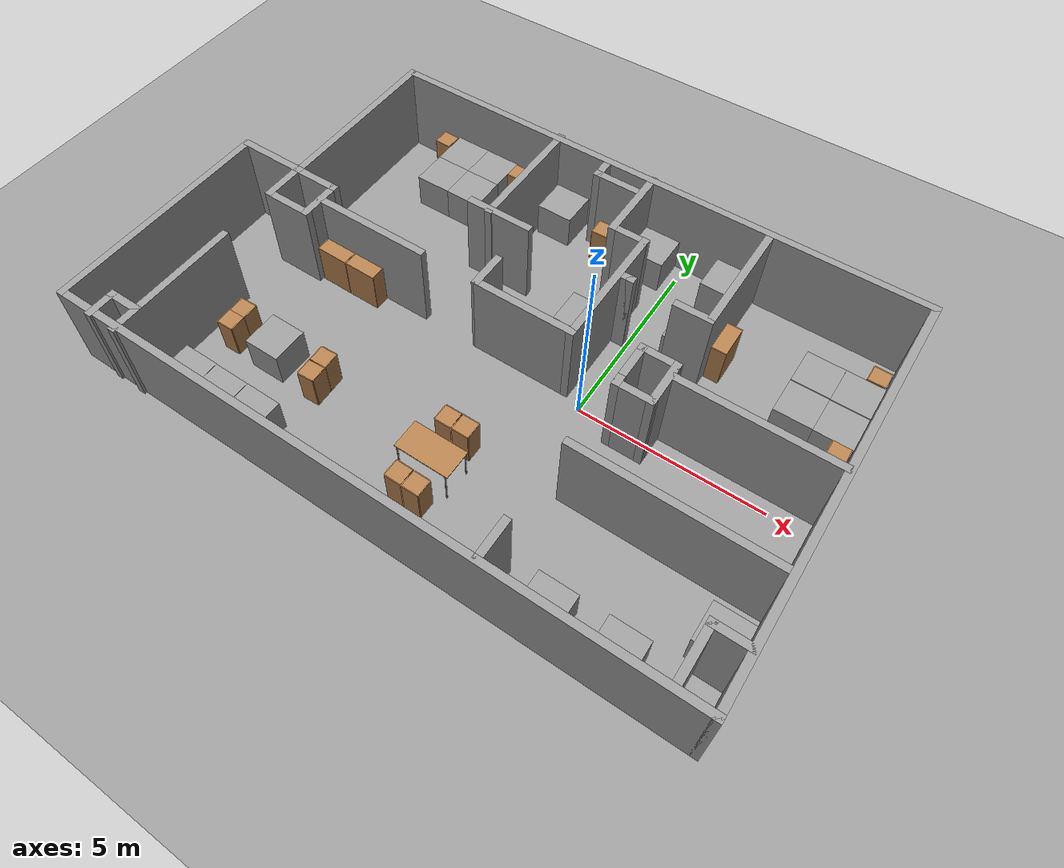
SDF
<sdf version="1.4">
 <world name="default">
  <light name="sun" type="directional">
   <pose>0 0 10 0 -0 0</pose>
   <diffuse>0.8 0.8 0.8 1</diffuse>
   <specular>0.2 0.2 0.2 1</specular>
   <attenuation>
    <range>1000</range>
    <constant>0.9</constant>
    <linear>0.01</linear>
    <quadratic>0.001</quadratic>
   </attenuation>
   <direction>0.5 0.1 -0.9</direction>
  </light>
  <scene><ambient>0.4 0.4 0.4 1</ambient><background>0.7 0.7 0.7 1</background><shadows>1</shadows></scene>
  <physics type="ode">
   <max_step_size>0.01</max_step_size>
   <real_time_factor>1</real_time_factor>
   <real_time_update_rate>100</real_time_update_rate>
   <gravity>0 0 -9.8</gravity>
  </physics>
  <model name="ground_plane_0">
   <static>1</static>
   <link name="link">
    <collision name="collision">
     <geometry><plane><normal>0 0 1</normal><size>100 100</size></plane></geometry>
     <surface><friction><ode><mu>100</mu><mu2>50</mu2></ode></friction></surface>
    </collision>
    <visual name="visual">
     <cast_shadows>0</cast_shadows>
     <geometry><plane><normal>0 0 1</normal><size>100 100</size></plane></geometry>
     <material>
      <script><uri>file://media/materials/scripts/gazebo.material</uri><name>Gazebo/Grey</name></script>
     </material>
    </visual>
    <velocity_decay><linear>0</linear><angular>0</angular></velocity_decay>
   </link>
   <pose>0.497681 0 0 0 -0 0</pose>
  </model>
  <spherical_coordinates>
   <surface_model>EARTH_WGS84</surface_model>
   <latitude_deg>0</latitude_deg>
   <longitude_deg>0</longitude_deg>
   <elevation>0</elevation>
   <heading_deg>0</heading_deg>
  </spherical_coordinates>
  <model name="roy4">
   <link name="Wall_0">
    <collision name="Wall_0_Collision">
     <geometry><box><size>6.43031 0.2 2.5</size></box></geometry>
     <pose>0 0 1.25 0 -0 0</pose>
    </collision>
    <visual name="Wall_0_Visual">
     <pose>0 0 1.25 0 -0 0</pose>
     <geometry><box><size>6.43031 0.2 2.5</size></box></geometry>
     <material>
      <script><uri>file://media/materials/scripts/gazebo.material</uri><name>Gazebo/Grey</name></script>
     </material>
    </visual>
    <velocity_decay><linear>0</linear><angular>0</angular></velocity_decay>
    <pose>-17.0197 -4.40915 0 0 0 -1.5708</pose>
   </link>
   <link name="Wall_1">
    <collision name="Wall_1_Collision">
     <geometry><box><size>17.3127 0.2 2.5</size></box></geometry>
     <pose>0 0 1.25 0 -0 0</pose>
    </collision>
    <visual name="Wall_1_Visual">
     <pose>0 0 1.25 0 -0 0</pose>
     <geometry><box><size>17.3127 0.2 2.5</size></box></geometry>
     <material>
      <script><uri>file://media/materials/scripts/gazebo.material</uri><name>Gazebo/Grey</name></script>
     </material>
    </visual>
    <velocity_decay><linear>0</linear><angular>0</angular></velocity_decay>
    <pose>-8.46335 -7.52431 0 0 -0 0</pose>
   </link>
   <link name="Wall_11">
    <collision name="Wall_11_Collision">
     <geometry><box><size>3.74537 0.2 2.5</size></box></geometry>
     <pose>0 0 1.25 0 -0 0</pose>
    </collision>
    <visual name="Wall_11_Visual">
     <pose>0 0 1.25 0 -0 0</pose>
     <geometry><box><size>3.74537 0.2 2.5</size></box></geometry>
     <material>
      <script><uri>file://media/materials/scripts/gazebo.material</uri><name>Gazebo/Grey</name></script>
     </material>
    </visual>
    <velocity_decay><linear>0</linear><angular>0</angular></velocity_decay>
    <pose>-15.1992 -5.81781 0 0 0 -1.5708</pose>
   </link>
   <link name="Wall_13">
    <collision name="Wall_13_Collision">
     <geometry><box><size>1.26434 0.2 2.5</size></box></geometry>
     <pose>0 0 1.25 0 -0 0</pose>
    </collision>
    <visual name="Wall_13_Visual">
     <pose>0 0 1.25 0 -0 0</pose>
     <geometry><box><size>1.26434 0.2 2.5</size></box></geometry>
     <material>
      <script><uri>file://media/materials/scripts/gazebo.material</uri><name>Gazebo/Grey</name></script>
     </material>
    </visual>
    <velocity_decay><linear>0</linear><angular>0</angular></velocity_decay>
    <pose>-15.2322 -1.76883 0 0 0 -1.5708</pose>
   </link>
   <link name="Wall_19">
    <collision name="Wall_19_Collision">
     <geometry><box><size>3.5068 0.2 2.5</size></box></geometry>
     <pose>0 0 1.25 0 -0 0</pose>
    </collision>
    <visual name="Wall_19_Visual">
     <pose>0 0 1.25 0 -0 0</pose>
     <geometry><box><size>3.5068 0.2 2.5</size></box></geometry>
     <material>
      <script><uri>file://media/materials/scripts/gazebo.material</uri><name>Gazebo/Grey</name></script>
     </material>
    </visual>
    <velocity_decay><linear>0</linear><angular>0</angular></velocity_decay>
    <pose>-10.2614 2.01073 0 0 0 -1.5708</pose>
   </link>
   <link name="Wall_2">
    <collision name="Wall_2_Collision">
     <geometry><box><size>11.3253 0.2 2.5</size></box></geometry>
     <pose>0 0 1.25 0 -0 0</pose>
    </collision>
    <visual name="Wall_2_Visual">
     <pose>0 0 1.25 0 -0 0</pose>
     <geometry><box><size>11.3253 0.2 2.5</size></box></geometry>
     <material>
      <script><uri>file://media/materials/scripts/gazebo.material</uri><name>Gazebo/Grey</name></script>
     </material>
    </visual>
    <velocity_decay><linear>0</linear><angular>0</angular></velocity_decay>
    <pose>0.093002 -1.96166 0 0 -0 1.5708</pose>
   </link>
   <link name="Wall_21">
    <collision name="Wall_21_Collision">
     <geometry><box><size>1.868 0.2 2.5</size></box></geometry>
     <pose>0 0 1.25 0 -0 0</pose>
    </collision>
    <visual name="Wall_21_Visual">
     <pose>0 0 1.25 0 -0 0</pose>
     <geometry><box><size>1.868 0.2 2.5</size></box></geometry>
     <material>
      <script><uri>file://media/materials/scripts/gazebo.material</uri><name>Gazebo/Grey</name></script>
     </material>
    </visual>
    <velocity_decay><linear>0</linear><angular>0</angular></velocity_decay>
    <pose>-9.9903 0.392512 0 0 -0 0</pose>
   </link>
   <link name="Wall_23">
    <collision name="Wall_23_Collision">
     <geometry><box><size>4.25711 0.2 2.5</size></box></geometry>
     <pose>0 0 1.25 0 -0 0</pose>
    </collision>
    <visual name="Wall_23_Visual">
     <pose>0 0 1.25 0 -0 0</pose>
     <geometry><box><size>4.25711 0.2 2.5</size></box></geometry>
     <material>
      <script><uri>file://media/materials/scripts/gazebo.material</uri><name>Gazebo/Grey</name></script>
     </material>
    </visual>
    <velocity_decay><linear>0</linear><angular>0</angular></velocity_decay>
    <pose>-1.94744 -1.54232 0 0 -0 3.14159</pose>
   </link>
   <link name="Wall_25">
    <collision name="Wall_25_Collision">
     <geometry><box><size>1.3609 0.2 2.5</size></box></geometry>
     <pose>0 0 1.25 0 -0 0</pose>
    </collision>
    <visual name="Wall_25_Visual">
     <pose>0 0 1.25 0 -0 0</pose>
     <geometry><box><size>1.3609 0.2 2.5</size></box></geometry>
     <material>
      <script><uri>file://media/materials/scripts/gazebo.material</uri><name>Gazebo/Grey</name></script>
     </material>
    </visual>
    <velocity_decay><linear>0</linear><angular>0</angular></velocity_decay>
    <pose>-14.606 -1.26089 0 0 -0 0</pose>
   </link>
   <link name="Wall_26">
    <collision name="Wall_26_Collision">
     <geometry><box><size>1.25536 0.2 2.5</size></box></geometry>
     <pose>0 0 1.25 0 -0 0</pose>
    </collision>
    <visual name="Wall_26_Visual">
     <pose>0 0 1.25 0 -0 0</pose>
     <geometry><box><size>1.25536 0.2 2.5</size></box></geometry>
     <material>
      <script><uri>file://media/materials/scripts/gazebo.material</uri><name>Gazebo/Grey</name></script>
     </material>
    </visual>
    <velocity_decay><linear>0</linear><angular>0</angular></velocity_decay>
    <pose>-14.0256 -1.78857 0 0 0 -1.5708</pose>
   </link>
   <link name="Wall_27">
    <collision name="Wall_27_Collision">
     <geometry><box><size>1.39608 0.2 2.5</size></box></geometry>
     <pose>0 0 1.25 0 -0 0</pose>
    </collision>
    <visual name="Wall_27_Visual">
     <pose>0 0 1.25 0 -0 0</pose>
     <geometry><box><size>1.39608 0.2 2.5</size></box></geometry>
     <material>
      <script><uri>file://media/materials/scripts/gazebo.material</uri><name>Gazebo/Grey</name></script>
     </material>
    </visual>
    <velocity_decay><linear>0</linear><angular>0</angular></velocity_decay>
    <pose>-14.6236 -2.31625 0 0 -0 3.14159</pose>
   </link>
   <link name="Wall_29">
    <collision name="Wall_29_Collision">
     <geometry><box><size>3.33091 0.2 2.5</size></box></geometry>
     <pose>0 0 1.25 0 -0 0</pose>
    </collision>
    <visual name="Wall_29_Visual">
     <pose>0 0 1.25 0 -0 0</pose>
     <geometry><box><size>3.33091 0.2 2.5</size></box></geometry>
     <material>
      <script><uri>file://media/materials/scripts/gazebo.material</uri><name>Gazebo/Grey</name></script>
     </material>
    </visual>
    <velocity_decay><linear>0</linear><angular>0</angular></velocity_decay>
    <pose>-12.4249 -1.75339 0 0 -0 0</pose>
   </link>
   <link name="Wall_3">
    <collision name="Wall_3_Collision">
     <geometry><box><size>15.3708 0.2 2.5</size></box></geometry>
     <pose>0 0 1.25 0 -0 0</pose>
    </collision>
    <visual name="Wall_3_Visual">
     <pose>0 0 1.25 0 -0 0</pose>
     <geometry><box><size>15.3708 0.2 2.5</size></box></geometry>
     <material>
      <script><uri>file://media/materials/scripts/gazebo.material</uri><name>Gazebo/Grey</name></script>
     </material>
    </visual>
    <velocity_decay><linear>0</linear><angular>0</angular></velocity_decay>
    <pose>-7.49242 3.60098 0 0 -0 3.14159</pose>
   </link>
   <link name="Wall_31">
    <collision name="Wall_31_Collision">
     <geometry><box><size>2.77907 0.2 2.5</size></box></geometry>
     <pose>0 0 1.25 0 -0 0</pose>
    </collision>
    <visual name="Wall_31_Visual">
     <pose>0 0 1.25 0 -0 0</pose>
     <geometry><box><size>2.77907 0.2 2.5</size></box></geometry>
     <material>
      <script><uri>file://media/materials/scripts/gazebo.material</uri><name>Gazebo/Grey</name></script>
     </material>
    </visual>
    <velocity_decay><linear>0</linear><angular>0</angular></velocity_decay>
    <pose>-7.82203 -1.75339 0 0 -0 0</pose>
   </link>
   <link name="Wall_32">
    <collision name="Wall_32_Collision">
     <geometry><box><size>3.57716 0.2 2.5</size></box></geometry>
     <pose>0 0 1.25 0 -0 0</pose>
    </collision>
    <visual name="Wall_32_Visual">
     <pose>0 0 1.25 0 -0 0</pose>
     <geometry><box><size>3.57716 0.2 2.5</size></box></geometry>
     <material>
      <script><uri>file://media/materials/scripts/gazebo.material</uri><name>Gazebo/Grey</name></script>
     </material>
    </visual>
    <velocity_decay><linear>0</linear><angular>0</angular></velocity_decay>
    <pose>-6.53249 -0.064812 0 0 -0 1.5708</pose>
   </link>
   <link name="Wall_33">
    <collision name="Wall_33_Collision">
     <geometry><box><size>1.07947 0.2 2.5</size></box></geometry>
     <pose>0 0 1.25 0 -0 0</pose>
    </collision>
    <visual name="Wall_33_Visual">
     <pose>0 0 1.25 0 -0 0</pose>
     <geometry><box><size>1.07947 0.2 2.5</size></box></geometry>
     <material>
      <script><uri>file://media/materials/scripts/gazebo.material</uri><name>Gazebo/Grey</name></script>
     </material>
    </visual>
    <velocity_decay><linear>0</linear><angular>0</angular></velocity_decay>
    <pose>-6.97223 1.62377 0 0 -0 3.14159</pose>
   </link>
   <link name="Wall_34">
    <collision name="Wall_34_Collision">
     <geometry><box><size>2.20642 0.2 2.5</size></box></geometry>
     <pose>0 0 1.25 0 -0 0</pose>
    </collision>
    <visual name="Wall_34_Visual">
     <pose>0 0 1.25 0 -0 0</pose>
     <geometry><box><size>2.20642 0.2 2.5</size></box></geometry>
     <material>
      <script><uri>file://media/materials/scripts/gazebo.material</uri><name>Gazebo/Grey</name></script>
     </material>
    </visual>
    <velocity_decay><linear>0</linear><angular>0</angular></velocity_decay>
    <pose>-7.41196 2.62652 0 0 -0 1.5708</pose>
   </link>
   <link name="Wall_36">
    <collision name="Wall_36_Collision">
     <geometry><box><size>0.732004 0.2 2.5</size></box></geometry>
     <pose>0 0 1.25 0 -0 0</pose>
    </collision>
    <visual name="Wall_36_Visual">
     <pose>0 0 1.25 0 -0 0</pose>
     <geometry><box><size>0.732004 0.2 2.5</size></box></geometry>
     <material>
      <script><uri>file://media/materials/scripts/gazebo.material</uri><name>Gazebo/Grey</name></script>
     </material>
    </visual>
    <velocity_decay><linear>0</linear><angular>0</angular></velocity_decay>
    <pose>-8.69464 3.30855 0 0 0 -1.5708</pose>
   </link>
   <link name="Wall_37">
    <collision name="Wall_37_Collision">
     <geometry><box><size>1.47218 0.2 2.5</size></box></geometry>
     <pose>0 0 1.25 0 -0 0</pose>
    </collision>
    <visual name="Wall_37_Visual">
     <pose>0 0 1.25 0 -0 0</pose>
     <geometry><box><size>1.47218 0.2 2.5</size></box></geometry>
     <material>
      <script><uri>file://media/materials/scripts/gazebo.material</uri><name>Gazebo/Grey</name></script>
     </material>
    </visual>
    <velocity_decay><linear>0</linear><angular>0</angular></velocity_decay>
    <pose>-8.05855 3.04255 0 0 -0 0</pose>
   </link>
   <link name="Wall_41">
    <collision name="Wall_41_Collision">
     <geometry><box><size>1.05583 0.2 2.5</size></box></geometry>
     <pose>0 0 1.25 0 -0 0</pose>
    </collision>
    <visual name="Wall_41_Visual">
     <pose>0 0 1.25 0 -0 0</pose>
     <geometry><box><size>1.05583 0.2 2.5</size></box></geometry>
     <material>
      <script><uri>file://media/materials/scripts/gazebo.material</uri><name>Gazebo/Grey</name></script>
     </material>
    </visual>
    <velocity_decay><linear>0</linear><angular>0</angular></velocity_decay>
    <pose>-9.18038 -1.31757 0 0 -0 1.5708</pose>
   </link>
   <link name="Wall_43">
    <collision name="Wall_43_Collision">
     <geometry><box><size>0.523829 0.2 2.5</size></box></geometry>
     <pose>0 0 1.25 0 -0 0</pose>
    </collision>
    <visual name="Wall_43_Visual">
     <pose>0 0 1.25 0 -0 0</pose>
     <geometry><box><size>0.523829 0.2 2.5</size></box></geometry>
     <material>
      <script><uri>file://media/materials/scripts/gazebo.material</uri><name>Gazebo/Grey</name></script>
     </material>
    </visual>
    <velocity_decay><linear>0</linear><angular>0</angular></velocity_decay>
    <pose>-6.35845 0.382531 0 0 -0 0</pose>
   </link>
   <link name="Wall_44">
    <collision name="Wall_44_Collision">
     <geometry><box><size>0.21 0.2 2.5</size></box></geometry>
     <pose>0 0 1.25 0 -0 0</pose>
    </collision>
    <visual name="Wall_44_Visual">
     <pose>0 0 1.25 0 -0 0</pose>
     <geometry><box><size>0.21 0.2 2.5</size></box></geometry>
     <material>
      <script><uri>file://media/materials/scripts/gazebo.material</uri><name>Gazebo/Grey</name></script>
     </material>
    </visual>
    <velocity_decay><linear>0</linear><angular>0</angular></velocity_decay>
    <pose>-6.19154 0.382531 0 0 -0 0</pose>
   </link>
   <link name="Wall_46">
    <collision name="Wall_46_Collision">
     <geometry><box><size>1.05614 0.2 2.5</size></box></geometry>
     <pose>0 0 1.25 0 -0 0</pose>
    </collision>
    <visual name="Wall_46_Visual">
     <pose>0 0 1.25 0 -0 0</pose>
     <geometry><box><size>1.05614 0.2 2.5</size></box></geometry>
     <material>
      <script><uri>file://media/materials/scripts/gazebo.material</uri><name>Gazebo/Grey</name></script>
     </material>
    </visual>
    <velocity_decay><linear>0</linear><angular>0</angular></velocity_decay>
    <pose>-4.49659 0.33627 0 0 -0 0</pose>
   </link>
   <link name="Wall_47">
    <collision name="Wall_47_Collision">
     <geometry><box><size>3.46142 0.2 2.5</size></box></geometry>
     <pose>0 0 1.25 0 -0 0</pose>
    </collision>
    <visual name="Wall_47_Visual">
     <pose>0 0 1.25 0 -0 0</pose>
     <geometry><box><size>3.46142 0.2 2.5</size></box></geometry>
     <material>
      <script><uri>file://media/materials/scripts/gazebo.material</uri><name>Gazebo/Grey</name></script>
     </material>
    </visual>
    <velocity_decay><linear>0</linear><angular>0</angular></velocity_decay>
    <pose>-4.06852 1.96698 0 0 -0 1.5708</pose>
   </link>
   <link name="Wall_5">
    <collision name="Wall_5_Collision">
     <geometry><box><size>1.98005 0.2 2.5</size></box></geometry>
     <pose>0 0 1.25 0 -0 0</pose>
    </collision>
    <visual name="Wall_5_Visual">
     <pose>0 0 1.25 0 -0 0</pose>
     <geometry><box><size>1.98005 0.2 2.5</size></box></geometry>
     <material>
      <script><uri>file://media/materials/scripts/gazebo.material</uri><name>Gazebo/Grey</name></script>
     </material>
    </visual>
    <velocity_decay><linear>0</linear><angular>0</angular></velocity_decay>
    <pose>-16.0892 -1.25369 0 0 -0 0</pose>
   </link>
   <link name="Wall_51">
    <collision name="Wall_51_Collision">
     <geometry><box><size>1.34428 0.2 2.5</size></box></geometry>
     <pose>0 0 1.25 0 -0 0</pose>
    </collision>
    <visual name="Wall_51_Visual">
     <pose>0 0 1.25 0 -0 0</pose>
     <geometry><box><size>1.34428 0.2 2.5</size></box></geometry>
     <material>
      <script><uri>file://media/materials/scripts/gazebo.material</uri><name>Gazebo/Grey</name></script>
     </material>
    </visual>
    <velocity_decay><linear>0</linear><angular>0</angular></velocity_decay>
    <pose>-4.10199 -1.80601 0 0 -0 1.57185</pose>
   </link>
   <link name="Wall_52">
    <collision name="Wall_52_Collision">
     <geometry><box><size>1.07781 0.2 2.5</size></box></geometry>
     <pose>0 0 1.25 0 -0 0</pose>
    </collision>
    <visual name="Wall_52_Visual">
     <pose>0 0 1.25 0 -0 0</pose>
     <geometry><box><size>1.07781 0.2 2.5</size></box></geometry>
     <material>
      <script><uri>file://media/materials/scripts/gazebo.material</uri><name>Gazebo/Grey</name></script>
     </material>
    </visual>
    <velocity_decay><linear>0</linear><angular>0</angular></velocity_decay>
    <pose>-4.5415 -1.2341 0 0 -0 3.14159</pose>
   </link>
   <link name="Wall_53">
    <collision name="Wall_53_Collision">
     <geometry><box><size>1.21081 0.2 2.5</size></box></geometry>
     <pose>0 0 1.25 0 -0 0</pose>
    </collision>
    <visual name="Wall_53_Visual">
     <pose>0 0 1.25 0 -0 0</pose>
     <geometry><box><size>1.21081 0.2 2.5</size></box></geometry>
     <material>
      <script><uri>file://media/materials/scripts/gazebo.material</uri><name>Gazebo/Grey</name></script>
     </material>
    </visual>
    <velocity_decay><linear>0</linear><angular>0</angular></velocity_decay>
    <pose>-4.9804 -1.73951 0 0 0 -1.5708</pose>
   </link>
   <link name="Wall_54">
    <collision name="Wall_54_Collision">
     <geometry><box><size>0.333001 0.2 2.5</size></box></geometry>
     <pose>0 0 1.25 0 -0 0</pose>
    </collision>
    <visual name="Wall_54_Visual">
     <pose>0 0 1.25 0 -0 0</pose>
     <geometry><box><size>0.333001 0.2 2.5</size></box></geometry>
     <material>
      <script><uri>file://media/materials/scripts/gazebo.material</uri><name>Gazebo/Grey</name></script>
     </material>
    </visual>
    <velocity_decay><linear>0</linear><angular>0</angular></velocity_decay>
    <pose>-4.9804 -2.31141 0 0 0 -1.5708</pose>
   </link>
   <link name="Wall_55">
    <collision name="Wall_55_Collision">
     <geometry><box><size>1.07902 0.2 2.5</size></box></geometry>
     <pose>0 0 1.25 0 -0 0</pose>
    </collision>
    <visual name="Wall_55_Visual">
     <pose>0 0 1.25 0 -0 0</pose>
     <geometry><box><size>1.07902 0.2 2.5</size></box></geometry>
     <material>
      <script><uri>file://media/materials/scripts/gazebo.material</uri><name>Gazebo/Grey</name></script>
     </material>
    </visual>
    <velocity_decay><linear>0</linear><angular>0</angular></velocity_decay>
    <pose>-4.54089 -2.37791 0 0 -0 0</pose>
   </link>
   <link name="Wall_57">
    <collision name="Wall_57_Collision">
     <geometry><box><size>5.2974 0.2 2.5</size></box></geometry>
     <pose>0 0 1.25 0 -0 0</pose>
    </collision>
    <visual name="Wall_57_Visual">
     <pose>0 0 1.25 0 -0 0</pose>
     <geometry><box><size>5.2974 0.2 2.5</size></box></geometry>
     <material>
      <script><uri>file://media/materials/scripts/gazebo.material</uri><name>Gazebo/Grey</name></script>
     </material>
    </visual>
    <velocity_decay><linear>0</linear><angular>0</angular></velocity_decay>
    <pose>-2.50218 -4.27298 0 0 -0 3.14159</pose>
   </link>
   <link name="Wall_59">
    <collision name="Wall_59_Collision">
     <geometry><box><size>1.11465 0.2 2.5</size></box></geometry>
     <pose>0 0 1.25 0 -0 0</pose>
    </collision>
    <visual name="Wall_59_Visual">
     <pose>0 0 1.25 0 -0 0</pose>
     <geometry><box><size>1.11465 0.2 2.5</size></box></geometry>
     <material>
      <script><uri>file://media/materials/scripts/gazebo.material</uri><name>Gazebo/Grey</name></script>
     </material>
    </visual>
    <velocity_decay><linear>0</linear><angular>0</angular></velocity_decay>
    <pose>-5.11669 -6.98224 0 0 -0 1.5708</pose>
   </link>
   <link name="Wall_6">
    <collision name="Wall_6_Collision">
     <geometry><box><size>5.05467 0.2 2.5</size></box></geometry>
     <pose>0 0 1.25 0 -0 0</pose>
    </collision>
    <visual name="Wall_6_Visual">
     <pose>0 0 1.25 0 -0 0</pose>
     <geometry><box><size>5.05467 0.2 2.5</size></box></geometry>
     <material>
      <script><uri>file://media/materials/scripts/gazebo.material</uri><name>Gazebo/Grey</name></script>
     </material>
    </visual>
    <velocity_decay><linear>0</linear><angular>0</angular></velocity_decay>
    <pose>-15.1992 1.17364 0 0 -0 1.5708</pose>
   </link>
   <link name="Wall_61">
    <collision name="Wall_61_Collision">
     <geometry><box><size>0.973933 0.2 2.5</size></box></geometry>
     <pose>0 0 1.25 0 -0 0</pose>
    </collision>
    <visual name="Wall_61_Visual">
     <pose>0 0 1.25 0 -0 0</pose>
     <geometry><box><size>0.973933 0.2 2.5</size></box></geometry>
     <material>
      <script><uri>file://media/materials/scripts/gazebo.material</uri><name>Gazebo/Grey</name></script>
     </material>
    </visual>
    <velocity_decay><linear>0</linear><angular>0</angular></velocity_decay>
    <pose>-15.6 -6.91189 0 0 -0 3.14159</pose>
   </link>
   <link name="Wall_62">
    <collision name="Wall_62_Collision">
     <geometry><box><size>0.868396 0.2 2.5</size></box></geometry>
     <pose>0 0 1.25 0 -0 0</pose>
    </collision>
    <visual name="Wall_62_Visual">
     <pose>0 0 1.25 0 -0 0</pose>
     <geometry><box><size>0.868396 0.2 2.5</size></box></geometry>
     <material>
      <script><uri>file://media/materials/scripts/gazebo.material</uri><name>Gazebo/Grey</name></script>
     </material>
    </visual>
    <velocity_decay><linear>0</linear><angular>0</angular></velocity_decay>
    <pose>-15.9869 -7.24609 0 0 0 -1.5708</pose>
   </link>
   <link name="Wall_64">
    <collision name="Wall_64_Collision">
     <geometry><box><size>1.04429 0.2 2.5</size></box></geometry>
     <pose>0 0 1.25 0 -0 0</pose>
    </collision>
    <visual name="Wall_64_Visual">
     <pose>0 0 1.25 0 -0 0</pose>
     <geometry><box><size>1.04429 0.2 2.5</size></box></geometry>
     <material>
      <script><uri>file://media/materials/scripts/gazebo.material</uri><name>Gazebo/Grey</name></script>
     </material>
    </visual>
    <velocity_decay><linear>0</linear><angular>0</angular></velocity_decay>
    <pose>-0.367561 -6.0676 0 0 -0 3.14159</pose>
   </link>
   <link name="Wall_65">
    <collision name="Wall_65_Collision">
     <geometry><box><size>1.64233 0.2 2.5</size></box></geometry>
     <pose>0 0 1.25 0 -0 0</pose>
    </collision>
    <visual name="Wall_65_Visual">
     <pose>0 0 1.25 0 -0 0</pose>
     <geometry><box><size>1.64233 0.2 2.5</size></box></geometry>
     <material>
      <script><uri>file://media/materials/scripts/gazebo.material</uri><name>Gazebo/Grey</name></script>
     </material>
    </visual>
    <velocity_decay><linear>0</linear><angular>0</angular></velocity_decay>
    <pose>-0.789706 -6.78876 0 0 0 -1.5708</pose>
   </link>
   <static>1</static>
   <pose>6 2 0 0 -0 0</pose>
  </model>
  <model name="cabinet">
   <static>1</static>
   <link name="cabinet_bottom_plate">
    <inertial>
     <pose>0 0 -1 0 -0 0</pose>
     <inertia><ixx>2.05</ixx><ixy>0</ixy><ixz>0</ixz><iyy>2.05</iyy><iyz>0</iyz><izz>2.05</izz></inertia>
     <mass>25</mass>
    </inertial>
    <collision name="cabinet_bottom_plate_geom">
     <pose>0 0 0.01 0 -0 0</pose>
     <geometry><box><size>0.45 0.45 0.02</size></box></geometry>
    </collision>
    <visual name="cabinet_bottom_plate_geom_visual">
     <pose>0 0 0.01 0 -0 0</pose>
     <geometry><box><size>0.45 0.45 0.02</size></box></geometry>
     <material>
      <script><uri>file://media/materials/scripts/gazebo.material</uri><name>Gazebo/Wood</name></script>
     </material>
    </visual>
    <collision name="cabinet_bottom_plate_geom_cabinet_back_plate">
     <pose>0.235 0 0.51 0 -0 0</pose>
     <geometry><box><size>0.02 0.45 1.02</size></box></geometry>
    </collision>
    <visual name="cabinet_bottom_plate_geom_cabinet_back_plate_visual">
     <pose>0.235 0 0.51 0 -0 0</pose>
     <geometry><box><size>0.02 0.45 1.02</size></box></geometry>
     <material>
      <script><uri>file://media/materials/scripts/gazebo.material</uri><name>Gazebo/Wood</name></script>
     </material>
    </visual>
    <collision name="cabinet_bottom_plate_geom_cabinet_left_plate">
     <pose>0 0.235 0.51 0 -0 0</pose>
     <geometry><box><size>0.45 0.02 1.02</size></box></geometry>
    </collision>
    <visual name="cabinet_bottom_plate_geom_cabinet_left_plate_visual">
     <pose>0 0.235 0.51 0 -0 0</pose>
     <geometry><box><size>0.45 0.02 1.02</size></box></geometry>
     <material>
      <script><uri>file://media/materials/scripts/gazebo.material</uri><name>Gazebo/Wood</name></script>
     </material>
    </visual>
    <collision name="cabinet_bottom_plate_geom_cabinet_middle_plate">
     <pose>0 0 0.51 0 -0 0</pose>
     <geometry><box><size>0.45 0.45 0.02</size></box></geometry>
    </collision>
    <visual name="cabinet_bottom_plate_geom_cabinet_middle_plate_visual">
     <pose>0 0 0.51 0 -0 0</pose>
     <geometry><box><size>0.45 0.45 0.02</size></box></geometry>
     <material>
      <script><uri>file://media/materials/scripts/gazebo.material</uri><name>Gazebo/Wood</name></script>
     </material>
    </visual>
    <collision name="cabinet_bottom_plate_geom_cabinet_right_plate">
     <pose>0 -0.235 0.51 0 -0 0</pose>
     <geometry><box><size>0.45 0.02 1.02</size></box></geometry>
    </collision>
    <visual name="cabinet_bottom_plate_geom_cabinet_right_plate_visual">
     <pose>0 -0.235 0.51 0 -0 0</pose>
     <geometry><box><size>0.45 0.02 1.02</size></box></geometry>
     <material>
      <script><uri>file://media/materials/scripts/gazebo.material</uri><name>Gazebo/Wood</name></script>
     </material>
    </visual>
    <collision name="cabinet_bottom_plate_geom_cabinet_top_plate">
     <pose>0 0 1.01 0 -0 0</pose>
     <geometry><box><size>0.45 0.45 0.02</size></box></geometry>
    </collision>
    <visual name="cabinet_bottom_plate_geom_cabinet_top_plate_visual">
     <pose>0 0 1.01 0 -0 0</pose>
     <geometry><box><size>0.45 0.45 0.02</size></box></geometry>
     <material>
      <script><uri>file://media/materials/scripts/gazebo.material</uri><name>Gazebo/Wood</name></script>
     </material>
    </visual>
    <velocity_decay><linear>0</linear><angular>0</angular></velocity_decay>
   </link>
   <pose>-8.83739 -5.17737 0 0 -0 0</pose>
  </model>
  <model name="unit_box_1">
   <pose>-8.08426 -4.90317 0.5 0 -0 0</pose>
   <link name="link">
    <inertial>
     <mass>1</mass>
     <inertia><ixx>1</ixx><ixy>0</ixy><ixz>0</ixz><iyy>1</iyy><iyz>0</iyz><izz>1</izz></inertia>
    </inertial>
    <collision name="collision"><geometry><box><size>1 1 1</size></box></geometry></collision>
    <visual name="visual">
     <geometry><box><size>1 1 1</size></box></geometry>
     <material>
      <script><uri>file://media/materials/scripts/gazebo.material</uri><name>Gazebo/Grey</name></script>
     </material>
    </visual>
    <velocity_decay><linear>0</linear><angular>0</angular></velocity_decay>
   </link>
   <static>0</static>
  </model>
  <model name="unit_box_2_0">
   <pose>-7.07514 -4.91144 0.5 0 -0 0</pose>
   <link name="link">
    <inertial>
     <mass>1</mass>
     <inertia><ixx>1</ixx><ixy>0</ixy><ixz>0</ixz><iyy>1</iyy><iyz>0</iyz><izz>1</izz></inertia>
    </inertial>
    <collision name="collision"><geometry><box><size>1 1 1</size></box></geometry></collision>
    <visual name="visual">
     <geometry><box><size>1 1 1</size></box></geometry>
     <material>
      <script><uri>file://media/materials/scripts/gazebo.material</uri><name>Gazebo/Grey</name></script>
     </material>
    </visual>
    <velocity_decay><linear>0</linear><angular>0</angular></velocity_decay>
   </link>
   <static>0</static>
  </model>
  <model name="unit_box_3">
   <pose>-6.06883 -4.90812 0.5 -0 -0 -0</pose>
   <link name="link">
    <inertial>
     <mass>1</mass>
     <inertia><ixx>1</ixx><ixy>0</ixy><ixz>0</ixz><iyy>1</iyy><iyz>0</iyz><izz>1</izz></inertia>
    </inertial>
    <collision name="collision"><geometry><box><size>1 1 1</size></box></geometry></collision>
    <visual name="visual">
     <geometry><box><size>1 1 1</size></box></geometry>
     <material>
      <script><uri>file://media/materials/scripts/gazebo.material</uri><name>Gazebo/Grey</name></script>
     </material>
    </visual>
    <velocity_decay><linear>0</linear><angular>0</angular></velocity_decay>
   </link>
   <static>0</static>
  </model>
  <model name="cabinet_0">
   <static>1</static>
   <link name="cabinet_bottom_plate">
    <inertial>
     <pose>0 0 -1 0 -0 0</pose>
     <inertia><ixx>2.05</ixx><ixy>0</ixy><ixz>0</ixz><iyy>2.05</iyy><iyz>0</iyz><izz>2.05</izz></inertia>
     <mass>25</mass>
    </inertial>
    <collision name="cabinet_bottom_plate_geom">
     <pose>0 0 0.01 0 -0 0</pose>
     <geometry><box><size>0.45 0.45 0.02</size></box></geometry>
    </collision>
    <visual name="cabinet_bottom_plate_geom_visual">
     <pose>0 0 0.01 0 -0 0</pose>
     <geometry><box><size>0.45 0.45 0.02</size></box></geometry>
     <material>
      <script><uri>file://media/materials/scripts/gazebo.material</uri><name>Gazebo/Wood</name></script>
     </material>
    </visual>
    <collision name="cabinet_bottom_plate_geom_cabinet_back_plate">
     <pose>0.235 0 0.51 0 -0 0</pose>
     <geometry><box><size>0.02 0.45 1.02</size></box></geometry>
    </collision>
    <visual name="cabinet_bottom_plate_geom_cabinet_back_plate_visual">
     <pose>0.235 0 0.51 0 -0 0</pose>
     <geometry><box><size>0.02 0.45 1.02</size></box></geometry>
     <material>
      <script><uri>file://media/materials/scripts/gazebo.material</uri><name>Gazebo/Wood</name></script>
     </material>
    </visual>
    <collision name="cabinet_bottom_plate_geom_cabinet_left_plate">
     <pose>0 0.235 0.51 0 -0 0</pose>
     <geometry><box><size>0.45 0.02 1.02</size></box></geometry>
    </collision>
    <visual name="cabinet_bottom_plate_geom_cabinet_left_plate_visual">
     <pose>0 0.235 0.51 0 -0 0</pose>
     <geometry><box><size>0.45 0.02 1.02</size></box></geometry>
     <material>
      <script><uri>file://media/materials/scripts/gazebo.material</uri><name>Gazebo/Wood</name></script>
     </material>
    </visual>
    <collision name="cabinet_bottom_plate_geom_cabinet_middle_plate">
     <pose>0 0 0.51 0 -0 0</pose>
     <geometry><box><size>0.45 0.45 0.02</size></box></geometry>
    </collision>
    <visual name="cabinet_bottom_plate_geom_cabinet_middle_plate_visual">
     <pose>0 0 0.51 0 -0 0</pose>
     <geometry><box><size>0.45 0.45 0.02</size></box></geometry>
     <material>
      <script><uri>file://media/materials/scripts/gazebo.material</uri><name>Gazebo/Wood</name></script>
     </material>
    </visual>
    <collision name="cabinet_bottom_plate_geom_cabinet_right_plate">
     <pose>0 -0.235 0.51 0 -0 0</pose>
     <geometry><box><size>0.45 0.02 1.02</size></box></geometry>
    </collision>
    <visual name="cabinet_bottom_plate_geom_cabinet_right_plate_visual">
     <pose>0 -0.235 0.51 0 -0 0</pose>
     <geometry><box><size>0.45 0.02 1.02</size></box></geometry>
     <material>
      <script><uri>file://media/materials/scripts/gazebo.material</uri><name>Gazebo/Wood</name></script>
     </material>
    </visual>
    <collision name="cabinet_bottom_plate_geom_cabinet_top_plate">
     <pose>0 0 1.01 0 -0 0</pose>
     <geometry><box><size>0.45 0.45 0.02</size></box></geometry>
    </collision>
    <visual name="cabinet_bottom_plate_geom_cabinet_top_plate_visual">
     <pose>0 0 1.01 0 -0 0</pose>
     <geometry><box><size>0.45 0.45 0.02</size></box></geometry>
     <material>
      <script><uri>file://media/materials/scripts/gazebo.material</uri><name>Gazebo/Wood</name></script>
     </material>
    </visual>
    <velocity_decay><linear>0</linear><angular>0</angular></velocity_decay>
   </link>
   <pose>-5.34383 -5.1572 0 0 -0 0</pose>
  </model>
  <model name="unit_box_4_0">
   <pose>-7 -3 0.5 0 -0 0</pose>
   <link name="link">
    <inertial>
     <mass>1</mass>
     <inertia><ixx>1</ixx><ixy>0</ixy><ixz>0</ixz><iyy>1</iyy><iyz>0</iyz><izz>1</izz></inertia>
    </inertial>
    <collision name="collision"><geometry><box><size>1 1 1</size></box></geometry></collision>
    <visual name="visual">
     <geometry><box><size>1 1 1</size></box></geometry>
     <material>
      <script><uri>file://media/materials/scripts/gazebo.material</uri><name>Gazebo/Grey</name></script>
     </material>
    </visual>
    <velocity_decay><linear>0</linear><angular>0</angular></velocity_decay>
   </link>
   <static>0</static>
  </model>
  <model name="cabinet_1">
   <static>1</static>
   <link name="cabinet_bottom_plate">
    <inertial>
     <pose>0 0 -1 0 -0 0</pose>
     <inertia><ixx>2.05</ixx><ixy>0</ixy><ixz>0</ixz><iyy>2.05</iyy><iyz>0</iyz><izz>2.05</izz></inertia>
     <mass>25</mass>
    </inertial>
    <collision name="cabinet_bottom_plate_geom">
     <pose>0 0 0.01 0 -0 0</pose>
     <geometry><box><size>0.45 0.45 0.02</size></box></geometry>
    </collision>
    <visual name="cabinet_bottom_plate_geom_visual">
     <pose>0 0 0.01 0 -0 0</pose>
     <geometry><box><size>0.45 0.45 0.02</size></box></geometry>
     <material>
      <script><uri>file://media/materials/scripts/gazebo.material</uri><name>Gazebo/Wood</name></script>
     </material>
    </visual>
    <collision name="cabinet_bottom_plate_geom_cabinet_back_plate">
     <pose>0.235 0 0.51 0 -0 0</pose>
     <geometry><box><size>0.02 0.45 1.02</size></box></geometry>
    </collision>
    <visual name="cabinet_bottom_plate_geom_cabinet_back_plate_visual">
     <pose>0.235 0 0.51 0 -0 0</pose>
     <geometry><box><size>0.02 0.45 1.02</size></box></geometry>
     <material>
      <script><uri>file://media/materials/scripts/gazebo.material</uri><name>Gazebo/Wood</name></script>
     </material>
    </visual>
    <collision name="cabinet_bottom_plate_geom_cabinet_left_plate">
     <pose>0 0.235 0.51 0 -0 0</pose>
     <geometry><box><size>0.45 0.02 1.02</size></box></geometry>
    </collision>
    <visual name="cabinet_bottom_plate_geom_cabinet_left_plate_visual">
     <pose>0 0.235 0.51 0 -0 0</pose>
     <geometry><box><size>0.45 0.02 1.02</size></box></geometry>
     <material>
      <script><uri>file://media/materials/scripts/gazebo.material</uri><name>Gazebo/Wood</name></script>
     </material>
    </visual>
    <collision name="cabinet_bottom_plate_geom_cabinet_middle_plate">
     <pose>0 0 0.51 0 -0 0</pose>
     <geometry><box><size>0.45 0.45 0.02</size></box></geometry>
    </collision>
    <visual name="cabinet_bottom_plate_geom_cabinet_middle_plate_visual">
     <pose>0 0 0.51 0 -0 0</pose>
     <geometry><box><size>0.45 0.45 0.02</size></box></geometry>
     <material>
      <script><uri>file://media/materials/scripts/gazebo.material</uri><name>Gazebo/Wood</name></script>
     </material>
    </visual>
    <collision name="cabinet_bottom_plate_geom_cabinet_right_plate">
     <pose>0 -0.235 0.51 0 -0 0</pose>
     <geometry><box><size>0.45 0.02 1.02</size></box></geometry>
    </collision>
    <visual name="cabinet_bottom_plate_geom_cabinet_right_plate_visual">
     <pose>0 -0.235 0.51 0 -0 0</pose>
     <geometry><box><size>0.45 0.02 1.02</size></box></geometry>
     <material>
      <script><uri>file://media/materials/scripts/gazebo.material</uri><name>Gazebo/Wood</name></script>
     </material>
    </visual>
    <collision name="cabinet_bottom_plate_geom_cabinet_top_plate">
     <pose>0 0 1.01 0 -0 0</pose>
     <geometry><box><size>0.45 0.45 0.02</size></box></geometry>
    </collision>
    <visual name="cabinet_bottom_plate_geom_cabinet_top_plate_visual">
     <pose>0 0 1.01 0 -0 0</pose>
     <geometry><box><size>0.45 0.45 0.02</size></box></geometry>
     <material>
      <script><uri>file://media/materials/scripts/gazebo.material</uri><name>Gazebo/Wood</name></script>
     </material>
    </visual>
    <velocity_decay><linear>0</linear><angular>0</angular></velocity_decay>
   </link>
   <pose>-5.57746 -3.27376 0 0 0 -1.5274</pose>
  </model>
  <model name="cabinet_2">
   <static>1</static>
   <link name="cabinet_bottom_plate">
    <inertial>
     <pose>0 0 -1 0 -0 0</pose>
     <inertia><ixx>2.05</ixx><ixy>0</ixy><ixz>0</ixz><iyy>2.05</iyy><iyz>0</iyz><izz>2.05</izz></inertia>
     <mass>25</mass>
    </inertial>
    <collision name="cabinet_bottom_plate_geom">
     <pose>0 0 0.01 0 -0 0</pose>
     <geometry><box><size>0.45 0.45 0.02</size></box></geometry>
    </collision>
    <visual name="cabinet_bottom_plate_geom_visual">
     <pose>0 0 0.01 0 -0 0</pose>
     <geometry><box><size>0.45 0.45 0.02</size></box></geometry>
     <material>
      <script><uri>file://media/materials/scripts/gazebo.material</uri><name>Gazebo/Wood</name></script>
     </material>
    </visual>
    <collision name="cabinet_bottom_plate_geom_cabinet_back_plate">
     <pose>0.235 0 0.51 0 -0 0</pose>
     <geometry><box><size>0.02 0.45 1.02</size></box></geometry>
    </collision>
    <visual name="cabinet_bottom_plate_geom_cabinet_back_plate_visual">
     <pose>0.235 0 0.51 0 -0 0</pose>
     <geometry><box><size>0.02 0.45 1.02</size></box></geometry>
     <material>
      <script><uri>file://media/materials/scripts/gazebo.material</uri><name>Gazebo/Wood</name></script>
     </material>
    </visual>
    <collision name="cabinet_bottom_plate_geom_cabinet_left_plate">
     <pose>0 0.235 0.51 0 -0 0</pose>
     <geometry><box><size>0.45 0.02 1.02</size></box></geometry>
    </collision>
    <visual name="cabinet_bottom_plate_geom_cabinet_left_plate_visual">
     <pose>0 0.235 0.51 0 -0 0</pose>
     <geometry><box><size>0.45 0.02 1.02</size></box></geometry>
     <material>
      <script><uri>file://media/materials/scripts/gazebo.material</uri><name>Gazebo/Wood</name></script>
     </material>
    </visual>
    <collision name="cabinet_bottom_plate_geom_cabinet_middle_plate">
     <pose>0 0 0.51 0 -0 0</pose>
     <geometry><box><size>0.45 0.45 0.02</size></box></geometry>
    </collision>
    <visual name="cabinet_bottom_plate_geom_cabinet_middle_plate_visual">
     <pose>0 0 0.51 0 -0 0</pose>
     <geometry><box><size>0.45 0.45 0.02</size></box></geometry>
     <material>
      <script><uri>file://media/materials/scripts/gazebo.material</uri><name>Gazebo/Wood</name></script>
     </material>
    </visual>
    <collision name="cabinet_bottom_plate_geom_cabinet_right_plate">
     <pose>0 -0.235 0.51 0 -0 0</pose>
     <geometry><box><size>0.45 0.02 1.02</size></box></geometry>
    </collision>
    <visual name="cabinet_bottom_plate_geom_cabinet_right_plate_visual">
     <pose>0 -0.235 0.51 0 -0 0</pose>
     <geometry><box><size>0.45 0.02 1.02</size></box></geometry>
     <material>
      <script><uri>file://media/materials/scripts/gazebo.material</uri><name>Gazebo/Wood</name></script>
     </material>
    </visual>
    <collision name="cabinet_bottom_plate_geom_cabinet_top_plate">
     <pose>0 0 1.01 0 -0 0</pose>
     <geometry><box><size>0.45 0.45 0.02</size></box></geometry>
    </collision>
    <visual name="cabinet_bottom_plate_geom_cabinet_top_plate_visual">
     <pose>0 0 1.01 0 -0 0</pose>
     <geometry><box><size>0.45 0.45 0.02</size></box></geometry>
     <material>
      <script><uri>file://media/materials/scripts/gazebo.material</uri><name>Gazebo/Wood</name></script>
     </material>
    </visual>
    <velocity_decay><linear>0</linear><angular>0</angular></velocity_decay>
   </link>
   <pose>-5.59482 -2.80227 0 0 -0 1.61682</pose>
  </model>
  <model name="cabinet_3">
   <static>1</static>
   <link name="cabinet_bottom_plate">
    <inertial>
     <pose>0 0 -1 0 -0 0</pose>
     <inertia><ixx>2.05</ixx><ixy>0</ixy><ixz>0</ixz><iyy>2.05</iyy><iyz>0</iyz><izz>2.05</izz></inertia>
     <mass>25</mass>
    </inertial>
    <collision name="cabinet_bottom_plate_geom">
     <pose>0 0 0.01 0 -0 0</pose>
     <geometry><box><size>0.45 0.45 0.02</size></box></geometry>
    </collision>
    <visual name="cabinet_bottom_plate_geom_visual">
     <pose>0 0 0.01 0 -0 0</pose>
     <geometry><box><size>0.45 0.45 0.02</size></box></geometry>
     <material>
      <script><uri>file://media/materials/scripts/gazebo.material</uri><name>Gazebo/Wood</name></script>
     </material>
    </visual>
    <collision name="cabinet_bottom_plate_geom_cabinet_back_plate">
     <pose>0.235 0 0.51 0 -0 0</pose>
     <geometry><box><size>0.02 0.45 1.02</size></box></geometry>
    </collision>
    <visual name="cabinet_bottom_plate_geom_cabinet_back_plate_visual">
     <pose>0.235 0 0.51 0 -0 0</pose>
     <geometry><box><size>0.02 0.45 1.02</size></box></geometry>
     <material>
      <script><uri>file://media/materials/scripts/gazebo.material</uri><name>Gazebo/Wood</name></script>
     </material>
    </visual>
    <collision name="cabinet_bottom_plate_geom_cabinet_left_plate">
     <pose>0 0.235 0.51 0 -0 0</pose>
     <geometry><box><size>0.45 0.02 1.02</size></box></geometry>
    </collision>
    <visual name="cabinet_bottom_plate_geom_cabinet_left_plate_visual">
     <pose>0 0.235 0.51 0 -0 0</pose>
     <geometry><box><size>0.45 0.02 1.02</size></box></geometry>
     <material>
      <script><uri>file://media/materials/scripts/gazebo.material</uri><name>Gazebo/Wood</name></script>
     </material>
    </visual>
    <collision name="cabinet_bottom_plate_geom_cabinet_middle_plate">
     <pose>0 0 0.51 0 -0 0</pose>
     <geometry><box><size>0.45 0.45 0.02</size></box></geometry>
    </collision>
    <visual name="cabinet_bottom_plate_geom_cabinet_middle_plate_visual">
     <pose>0 0 0.51 0 -0 0</pose>
     <geometry><box><size>0.45 0.45 0.02</size></box></geometry>
     <material>
      <script><uri>file://media/materials/scripts/gazebo.material</uri><name>Gazebo/Wood</name></script>
     </material>
    </visual>
    <collision name="cabinet_bottom_plate_geom_cabinet_right_plate">
     <pose>0 -0.235 0.51 0 -0 0</pose>
     <geometry><box><size>0.45 0.02 1.02</size></box></geometry>
    </collision>
    <visual name="cabinet_bottom_plate_geom_cabinet_right_plate_visual">
     <pose>0 -0.235 0.51 0 -0 0</pose>
     <geometry><box><size>0.45 0.02 1.02</size></box></geometry>
     <material>
      <script><uri>file://media/materials/scripts/gazebo.material</uri><name>Gazebo/Wood</name></script>
     </material>
    </visual>
    <collision name="cabinet_bottom_plate_geom_cabinet_top_plate">
     <pose>0 0 1.01 0 -0 0</pose>
     <geometry><box><size>0.45 0.45 0.02</size></box></geometry>
    </collision>
    <visual name="cabinet_bottom_plate_geom_cabinet_top_plate_visual">
     <pose>0 0 1.01 0 -0 0</pose>
     <geometry><box><size>0.45 0.45 0.02</size></box></geometry>
     <material>
      <script><uri>file://media/materials/scripts/gazebo.material</uri><name>Gazebo/Wood</name></script>
     </material>
    </visual>
    <velocity_decay><linear>0</linear><angular>0</angular></velocity_decay>
   </link>
   <pose>-8.25711 -3.22617 0 0 0 -1.54762</pose>
  </model>
  <model name="cabinet_4">
   <static>1</static>
   <link name="cabinet_bottom_plate">
    <inertial>
     <pose>0 0 -1 0 -0 0</pose>
     <inertia><ixx>2.05</ixx><ixy>0</ixy><ixz>0</ixz><iyy>2.05</iyy><iyz>0</iyz><izz>2.05</izz></inertia>
     <mass>25</mass>
    </inertial>
    <collision name="cabinet_bottom_plate_geom">
     <pose>0 0 0.01 0 -0 0</pose>
     <geometry><box><size>0.45 0.45 0.02</size></box></geometry>
    </collision>
    <visual name="cabinet_bottom_plate_geom_visual">
     <pose>0 0 0.01 0 -0 0</pose>
     <geometry><box><size>0.45 0.45 0.02</size></box></geometry>
     <material>
      <script><uri>file://media/materials/scripts/gazebo.material</uri><name>Gazebo/Wood</name></script>
     </material>
    </visual>
    <collision name="cabinet_bottom_plate_geom_cabinet_back_plate">
     <pose>0.235 0 0.51 0 -0 0</pose>
     <geometry><box><size>0.02 0.45 1.02</size></box></geometry>
    </collision>
    <visual name="cabinet_bottom_plate_geom_cabinet_back_plate_visual">
     <pose>0.235 0 0.51 0 -0 0</pose>
     <geometry><box><size>0.02 0.45 1.02</size></box></geometry>
     <material>
      <script><uri>file://media/materials/scripts/gazebo.material</uri><name>Gazebo/Wood</name></script>
     </material>
    </visual>
    <collision name="cabinet_bottom_plate_geom_cabinet_left_plate">
     <pose>0 0.235 0.51 0 -0 0</pose>
     <geometry><box><size>0.45 0.02 1.02</size></box></geometry>
    </collision>
    <visual name="cabinet_bottom_plate_geom_cabinet_left_plate_visual">
     <pose>0 0.235 0.51 0 -0 0</pose>
     <geometry><box><size>0.45 0.02 1.02</size></box></geometry>
     <material>
      <script><uri>file://media/materials/scripts/gazebo.material</uri><name>Gazebo/Wood</name></script>
     </material>
    </visual>
    <collision name="cabinet_bottom_plate_geom_cabinet_middle_plate">
     <pose>0 0 0.51 0 -0 0</pose>
     <geometry><box><size>0.45 0.45 0.02</size></box></geometry>
    </collision>
    <visual name="cabinet_bottom_plate_geom_cabinet_middle_plate_visual">
     <pose>0 0 0.51 0 -0 0</pose>
     <geometry><box><size>0.45 0.45 0.02</size></box></geometry>
     <material>
      <script><uri>file://media/materials/scripts/gazebo.material</uri><name>Gazebo/Wood</name></script>
     </material>
    </visual>
    <collision name="cabinet_bottom_plate_geom_cabinet_right_plate">
     <pose>0 -0.235 0.51 0 -0 0</pose>
     <geometry><box><size>0.45 0.02 1.02</size></box></geometry>
    </collision>
    <visual name="cabinet_bottom_plate_geom_cabinet_right_plate_visual">
     <pose>0 -0.235 0.51 0 -0 0</pose>
     <geometry><box><size>0.45 0.02 1.02</size></box></geometry>
     <material>
      <script><uri>file://media/materials/scripts/gazebo.material</uri><name>Gazebo/Wood</name></script>
     </material>
    </visual>
    <collision name="cabinet_bottom_plate_geom_cabinet_top_plate">
     <pose>0 0 1.01 0 -0 0</pose>
     <geometry><box><size>0.45 0.45 0.02</size></box></geometry>
    </collision>
    <visual name="cabinet_bottom_plate_geom_cabinet_top_plate_visual">
     <pose>0 0 1.01 0 -0 0</pose>
     <geometry><box><size>0.45 0.45 0.02</size></box></geometry>
     <material>
      <script><uri>file://media/materials/scripts/gazebo.material</uri><name>Gazebo/Wood</name></script>
     </material>
    </visual>
    <velocity_decay><linear>0</linear><angular>0</angular></velocity_decay>
   </link>
   <pose>-8.25999 -2.78265 0 0 -0 1.59135</pose>
  </model>
  <model name="cabinet_5">
   <static>1</static>
   <link name="cabinet_bottom_plate">
    <inertial>
     <pose>0 0 -1 0 -0 0</pose>
     <inertia><ixx>2.05</ixx><ixy>0</ixy><ixz>0</ixz><iyy>2.05</iyy><iyz>0</iyz><izz>2.05</izz></inertia>
     <mass>25</mass>
    </inertial>
    <collision name="cabinet_bottom_plate_geom">
     <pose>0 0 0.01 0 -0 0</pose>
     <geometry><box><size>0.45 0.45 0.02</size></box></geometry>
    </collision>
    <visual name="cabinet_bottom_plate_geom_visual">
     <pose>0 0 0.01 0 -0 0</pose>
     <geometry><box><size>0.45 0.45 0.02</size></box></geometry>
     <material>
      <script><uri>file://media/materials/scripts/gazebo.material</uri><name>Gazebo/Wood</name></script>
     </material>
    </visual>
    <collision name="cabinet_bottom_plate_geom_cabinet_back_plate">
     <pose>0.235 0 0.51 0 -0 0</pose>
     <geometry><box><size>0.02 0.45 1.02</size></box></geometry>
    </collision>
    <visual name="cabinet_bottom_plate_geom_cabinet_back_plate_visual">
     <pose>0.235 0 0.51 0 -0 0</pose>
     <geometry><box><size>0.02 0.45 1.02</size></box></geometry>
     <material>
      <script><uri>file://media/materials/scripts/gazebo.material</uri><name>Gazebo/Wood</name></script>
     </material>
    </visual>
    <collision name="cabinet_bottom_plate_geom_cabinet_left_plate">
     <pose>0 0.235 0.51 0 -0 0</pose>
     <geometry><box><size>0.45 0.02 1.02</size></box></geometry>
    </collision>
    <visual name="cabinet_bottom_plate_geom_cabinet_left_plate_visual">
     <pose>0 0.235 0.51 0 -0 0</pose>
     <geometry><box><size>0.45 0.02 1.02</size></box></geometry>
     <material>
      <script><uri>file://media/materials/scripts/gazebo.material</uri><name>Gazebo/Wood</name></script>
     </material>
    </visual>
    <collision name="cabinet_bottom_plate_geom_cabinet_middle_plate">
     <pose>0 0 0.51 0 -0 0</pose>
     <geometry><box><size>0.45 0.45 0.02</size></box></geometry>
    </collision>
    <visual name="cabinet_bottom_plate_geom_cabinet_middle_plate_visual">
     <pose>0 0 0.51 0 -0 0</pose>
     <geometry><box><size>0.45 0.45 0.02</size></box></geometry>
     <material>
      <script><uri>file://media/materials/scripts/gazebo.material</uri><name>Gazebo/Wood</name></script>
     </material>
    </visual>
    <collision name="cabinet_bottom_plate_geom_cabinet_right_plate">
     <pose>0 -0.235 0.51 0 -0 0</pose>
     <geometry><box><size>0.45 0.02 1.02</size></box></geometry>
    </collision>
    <visual name="cabinet_bottom_plate_geom_cabinet_right_plate_visual">
     <pose>0 -0.235 0.51 0 -0 0</pose>
     <geometry><box><size>0.45 0.02 1.02</size></box></geometry>
     <material>
      <script><uri>file://media/materials/scripts/gazebo.material</uri><name>Gazebo/Wood</name></script>
     </material>
    </visual>
    <collision name="cabinet_bottom_plate_geom_cabinet_top_plate">
     <pose>0 0 1.01 0 -0 0</pose>
     <geometry><box><size>0.45 0.45 0.02</size></box></geometry>
    </collision>
    <visual name="cabinet_bottom_plate_geom_cabinet_top_plate_visual">
     <pose>0 0 1.01 0 -0 0</pose>
     <geometry><box><size>0.45 0.45 0.02</size></box></geometry>
     <material>
      <script><uri>file://media/materials/scripts/gazebo.material</uri><name>Gazebo/Wood</name></script>
     </material>
    </visual>
    <velocity_decay><linear>0</linear><angular>0</angular></velocity_decay>
   </link>
   <pose>-2.13888 -4.27539 0 0 -0 3.13178</pose>
  </model>
  <model name="cabinet_6">
   <static>1</static>
   <link name="cabinet_bottom_plate">
    <inertial>
     <pose>0 0 -1 0 -0 0</pose>
     <inertia><ixx>2.05</ixx><ixy>0</ixy><ixz>0</ixz><iyy>2.05</iyy><iyz>0</iyz><izz>2.05</izz></inertia>
     <mass>25</mass>
    </inertial>
    <collision name="cabinet_bottom_plate_geom">
     <pose>0 0 0.01 0 -0 0</pose>
     <geometry><box><size>0.45 0.45 0.02</size></box></geometry>
    </collision>
    <visual name="cabinet_bottom_plate_geom_visual">
     <pose>0 0 0.01 0 -0 0</pose>
     <geometry><box><size>0.45 0.45 0.02</size></box></geometry>
     <material>
      <script><uri>file://media/materials/scripts/gazebo.material</uri><name>Gazebo/Wood</name></script>
     </material>
    </visual>
    <collision name="cabinet_bottom_plate_geom_cabinet_back_plate">
     <pose>0.235 0 0.51 0 -0 0</pose>
     <geometry><box><size>0.02 0.45 1.02</size></box></geometry>
    </collision>
    <visual name="cabinet_bottom_plate_geom_cabinet_back_plate_visual">
     <pose>0.235 0 0.51 0 -0 0</pose>
     <geometry><box><size>0.02 0.45 1.02</size></box></geometry>
     <material>
      <script><uri>file://media/materials/scripts/gazebo.material</uri><name>Gazebo/Wood</name></script>
     </material>
    </visual>
    <collision name="cabinet_bottom_plate_geom_cabinet_left_plate">
     <pose>0 0.235 0.51 0 -0 0</pose>
     <geometry><box><size>0.45 0.02 1.02</size></box></geometry>
    </collision>
    <visual name="cabinet_bottom_plate_geom_cabinet_left_plate_visual">
     <pose>0 0.235 0.51 0 -0 0</pose>
     <geometry><box><size>0.45 0.02 1.02</size></box></geometry>
     <material>
      <script><uri>file://media/materials/scripts/gazebo.material</uri><name>Gazebo/Wood</name></script>
     </material>
    </visual>
    <collision name="cabinet_bottom_plate_geom_cabinet_middle_plate">
     <pose>0 0 0.51 0 -0 0</pose>
     <geometry><box><size>0.45 0.45 0.02</size></box></geometry>
    </collision>
    <visual name="cabinet_bottom_plate_geom_cabinet_middle_plate_visual">
     <pose>0 0 0.51 0 -0 0</pose>
     <geometry><box><size>0.45 0.45 0.02</size></box></geometry>
     <material>
      <script><uri>file://media/materials/scripts/gazebo.material</uri><name>Gazebo/Wood</name></script>
     </material>
    </visual>
    <collision name="cabinet_bottom_plate_geom_cabinet_right_plate">
     <pose>0 -0.235 0.51 0 -0 0</pose>
     <geometry><box><size>0.45 0.02 1.02</size></box></geometry>
    </collision>
    <visual name="cabinet_bottom_plate_geom_cabinet_right_plate_visual">
     <pose>0 -0.235 0.51 0 -0 0</pose>
     <geometry><box><size>0.45 0.02 1.02</size></box></geometry>
     <material>
      <script><uri>file://media/materials/scripts/gazebo.material</uri><name>Gazebo/Wood</name></script>
     </material>
    </visual>
    <collision name="cabinet_bottom_plate_geom_cabinet_top_plate">
     <pose>0 0 1.01 0 -0 0</pose>
     <geometry><box><size>0.45 0.45 0.02</size></box></geometry>
    </collision>
    <visual name="cabinet_bottom_plate_geom_cabinet_top_plate_visual">
     <pose>0 0 1.01 0 -0 0</pose>
     <geometry><box><size>0.45 0.45 0.02</size></box></geometry>
     <material>
      <script><uri>file://media/materials/scripts/gazebo.material</uri><name>Gazebo/Wood</name></script>
     </material>
    </visual>
    <velocity_decay><linear>0</linear><angular>0</angular></velocity_decay>
   </link>
   <pose>-1.65312 -4.27891 0 0 -0 0</pose>
  </model>
  <model name="cabinet_7">
   <static>1</static>
   <link name="cabinet_bottom_plate">
    <inertial>
     <pose>0 0 -1 0 -0 0</pose>
     <inertia><ixx>2.05</ixx><ixy>0</ixy><ixz>0</ixz><iyy>2.05</iyy><iyz>0</iyz><izz>2.05</izz></inertia>
     <mass>25</mass>
    </inertial>
    <collision name="cabinet_bottom_plate_geom">
     <pose>0 0 0.01 0 -0 0</pose>
     <geometry><box><size>0.45 0.45 0.02</size></box></geometry>
    </collision>
    <visual name="cabinet_bottom_plate_geom_visual">
     <pose>0 0 0.01 0 -0 0</pose>
     <geometry><box><size>0.45 0.45 0.02</size></box></geometry>
     <material>
      <script><uri>file://media/materials/scripts/gazebo.material</uri><name>Gazebo/Wood</name></script>
     </material>
    </visual>
    <collision name="cabinet_bottom_plate_geom_cabinet_back_plate">
     <pose>0.235 0 0.51 0 -0 0</pose>
     <geometry><box><size>0.02 0.45 1.02</size></box></geometry>
    </collision>
    <visual name="cabinet_bottom_plate_geom_cabinet_back_plate_visual">
     <pose>0.235 0 0.51 0 -0 0</pose>
     <geometry><box><size>0.02 0.45 1.02</size></box></geometry>
     <material>
      <script><uri>file://media/materials/scripts/gazebo.material</uri><name>Gazebo/Wood</name></script>
     </material>
    </visual>
    <collision name="cabinet_bottom_plate_geom_cabinet_left_plate">
     <pose>0 0.235 0.51 0 -0 0</pose>
     <geometry><box><size>0.45 0.02 1.02</size></box></geometry>
    </collision>
    <visual name="cabinet_bottom_plate_geom_cabinet_left_plate_visual">
     <pose>0 0.235 0.51 0 -0 0</pose>
     <geometry><box><size>0.45 0.02 1.02</size></box></geometry>
     <material>
      <script><uri>file://media/materials/scripts/gazebo.material</uri><name>Gazebo/Wood</name></script>
     </material>
    </visual>
    <collision name="cabinet_bottom_plate_geom_cabinet_middle_plate">
     <pose>0 0 0.51 0 -0 0</pose>
     <geometry><box><size>0.45 0.45 0.02</size></box></geometry>
    </collision>
    <visual name="cabinet_bottom_plate_geom_cabinet_middle_plate_visual">
     <pose>0 0 0.51 0 -0 0</pose>
     <geometry><box><size>0.45 0.45 0.02</size></box></geometry>
     <material>
      <script><uri>file://media/materials/scripts/gazebo.material</uri><name>Gazebo/Wood</name></script>
     </material>
    </visual>
    <collision name="cabinet_bottom_plate_geom_cabinet_right_plate">
     <pose>0 -0.235 0.51 0 -0 0</pose>
     <geometry><box><size>0.45 0.02 1.02</size></box></geometry>
    </collision>
    <visual name="cabinet_bottom_plate_geom_cabinet_right_plate_visual">
     <pose>0 -0.235 0.51 0 -0 0</pose>
     <geometry><box><size>0.45 0.02 1.02</size></box></geometry>
     <material>
      <script><uri>file://media/materials/scripts/gazebo.material</uri><name>Gazebo/Wood</name></script>
     </material>
    </visual>
    <collision name="cabinet_bottom_plate_geom_cabinet_top_plate">
     <pose>0 0 1.01 0 -0 0</pose>
     <geometry><box><size>0.45 0.45 0.02</size></box></geometry>
    </collision>
    <visual name="cabinet_bottom_plate_geom_cabinet_top_plate_visual">
     <pose>0 0 1.01 0 -0 0</pose>
     <geometry><box><size>0.45 0.45 0.02</size></box></geometry>
     <material>
      <script><uri>file://media/materials/scripts/gazebo.material</uri><name>Gazebo/Wood</name></script>
     </material>
    </visual>
    <velocity_decay><linear>0</linear><angular>0</angular></velocity_decay>
   </link>
   <pose>-2.09881 -2.45928 0 0 0 -3.12859</pose>
  </model>
  <model name="cabinet_8">
   <static>1</static>
   <link name="cabinet_bottom_plate">
    <inertial>
     <pose>0 0 -1 0 -0 0</pose>
     <inertia><ixx>2.05</ixx><ixy>0</ixy><ixz>0</ixz><iyy>2.05</iyy><iyz>0</iyz><izz>2.05</izz></inertia>
     <mass>25</mass>
    </inertial>
    <collision name="cabinet_bottom_plate_geom">
     <pose>0 0 0.01 0 -0 0</pose>
     <geometry><box><size>0.45 0.45 0.02</size></box></geometry>
    </collision>
    <visual name="cabinet_bottom_plate_geom_visual">
     <pose>0 0 0.01 0 -0 0</pose>
     <geometry><box><size>0.45 0.45 0.02</size></box></geometry>
     <material>
      <script><uri>file://media/materials/scripts/gazebo.material</uri><name>Gazebo/Wood</name></script>
     </material>
    </visual>
    <collision name="cabinet_bottom_plate_geom_cabinet_back_plate">
     <pose>0.235 0 0.51 0 -0 0</pose>
     <geometry><box><size>0.02 0.45 1.02</size></box></geometry>
    </collision>
    <visual name="cabinet_bottom_plate_geom_cabinet_back_plate_visual">
     <pose>0.235 0 0.51 0 -0 0</pose>
     <geometry><box><size>0.02 0.45 1.02</size></box></geometry>
     <material>
      <script><uri>file://media/materials/scripts/gazebo.material</uri><name>Gazebo/Wood</name></script>
     </material>
    </visual>
    <collision name="cabinet_bottom_plate_geom_cabinet_left_plate">
     <pose>0 0.235 0.51 0 -0 0</pose>
     <geometry><box><size>0.45 0.02 1.02</size></box></geometry>
    </collision>
    <visual name="cabinet_bottom_plate_geom_cabinet_left_plate_visual">
     <pose>0 0.235 0.51 0 -0 0</pose>
     <geometry><box><size>0.45 0.02 1.02</size></box></geometry>
     <material>
      <script><uri>file://media/materials/scripts/gazebo.material</uri><name>Gazebo/Wood</name></script>
     </material>
    </visual>
    <collision name="cabinet_bottom_plate_geom_cabinet_middle_plate">
     <pose>0 0 0.51 0 -0 0</pose>
     <geometry><box><size>0.45 0.45 0.02</size></box></geometry>
    </collision>
    <visual name="cabinet_bottom_plate_geom_cabinet_middle_plate_visual">
     <pose>0 0 0.51 0 -0 0</pose>
     <geometry><box><size>0.45 0.45 0.02</size></box></geometry>
     <material>
      <script><uri>file://media/materials/scripts/gazebo.material</uri><name>Gazebo/Wood</name></script>
     </material>
    </visual>
    <collision name="cabinet_bottom_plate_geom_cabinet_right_plate">
     <pose>0 -0.235 0.51 0 -0 0</pose>
     <geometry><box><size>0.45 0.02 1.02</size></box></geometry>
    </collision>
    <visual name="cabinet_bottom_plate_geom_cabinet_right_plate_visual">
     <pose>0 -0.235 0.51 0 -0 0</pose>
     <geometry><box><size>0.45 0.02 1.02</size></box></geometry>
     <material>
      <script><uri>file://media/materials/scripts/gazebo.material</uri><name>Gazebo/Wood</name></script>
     </material>
    </visual>
    <collision name="cabinet_bottom_plate_geom_cabinet_top_plate">
     <pose>0 0 1.01 0 -0 0</pose>
     <geometry><box><size>0.45 0.45 0.02</size></box></geometry>
    </collision>
    <visual name="cabinet_bottom_plate_geom_cabinet_top_plate_visual">
     <pose>0 0 1.01 0 -0 0</pose>
     <geometry><box><size>0.45 0.45 0.02</size></box></geometry>
     <material>
      <script><uri>file://media/materials/scripts/gazebo.material</uri><name>Gazebo/Wood</name></script>
     </material>
    </visual>
    <velocity_decay><linear>0</linear><angular>0</angular></velocity_decay>
   </link>
   <pose>-1.61386 -2.45287 0 0 -0 0</pose>
  </model>
  <model name="unit_box_6_0">
   <pose>-7 4.99999 0.5 -0 -0 -1.2e-05</pose>
   <link name="link">
    <inertial>
     <mass>1</mass>
     <inertia><ixx>1</ixx><ixy>0</ixy><ixz>0</ixz><iyy>1</iyy><iyz>0</iyz><izz>1</izz></inertia>
    </inertial>
    <collision name="collision"><geometry><box><size>1 1 1</size></box></geometry></collision>
    <visual name="visual">
     <geometry><box><size>1 1 1</size></box></geometry>
     <material>
      <script><uri>file://media/materials/scripts/gazebo.material</uri><name>Gazebo/Grey</name></script>
     </material>
    </visual>
    <velocity_decay><linear>0</linear><angular>0</angular></velocity_decay>
   </link>
   <static>0</static>
  </model>
  <model name="unit_box_7_0">
   <pose>-5.99991 5.00005 0.5 0 -0 -0.000104</pose>
   <link name="link">
    <inertial>
     <mass>1</mass>
     <inertia><ixx>1</ixx><ixy>0</ixy><ixz>0</ixz><iyy>1</iyy><iyz>0</iyz><izz>1</izz></inertia>
    </inertial>
    <collision name="collision"><geometry><box><size>1 1 1</size></box></geometry></collision>
    <visual name="visual">
     <geometry><box><size>1 1 1</size></box></geometry>
     <material>
      <script><uri>file://media/materials/scripts/gazebo.material</uri><name>Gazebo/Grey</name></script>
     </material>
    </visual>
    <velocity_decay><linear>0</linear><angular>0</angular></velocity_decay>
   </link>
   <static>0</static>
  </model>
  <model name="unit_box_8">
   <pose>-7.00003 3.99994 0.5 -0 -0 -1.5e-05</pose>
   <link name="link">
    <inertial>
     <mass>1</mass>
     <inertia><ixx>1</ixx><ixy>0</ixy><ixz>0</ixz><iyy>1</iyy><iyz>0</iyz><izz>1</izz></inertia>
    </inertial>
    <collision name="collision"><geometry><box><size>1 1 1</size></box></geometry></collision>
    <visual name="visual">
     <geometry><box><size>1 1 1</size></box></geometry>
     <material>
      <script><uri>file://media/materials/scripts/gazebo.material</uri><name>Gazebo/Grey</name></script>
     </material>
    </visual>
    <velocity_decay><linear>0</linear><angular>0</angular></velocity_decay>
   </link>
   <static>0</static>
  </model>
  <model name="unit_box_9_0">
   <pose>-6 3.99986 0.5 0 -0 1e-06</pose>
   <link name="link">
    <inertial>
     <mass>1</mass>
     <inertia><ixx>1</ixx><ixy>0</ixy><ixz>0</ixz><iyy>1</iyy><iyz>0</iyz><izz>1</izz></inertia>
    </inertial>
    <collision name="collision"><geometry><box><size>1 1 1</size></box></geometry></collision>
    <visual name="visual">
     <geometry><box><size>1 1 1</size></box></geometry>
     <material>
      <script><uri>file://media/materials/scripts/gazebo.material</uri><name>Gazebo/Grey</name></script>
     </material>
    </visual>
    <velocity_decay><linear>0</linear><angular>0</angular></velocity_decay>
   </link>
   <static>0</static>
  </model>
  <model name="cabinet_9">
   <static>1</static>
   <link name="cabinet_bottom_plate">
    <inertial>
     <pose>0 0 -1 0 -0 0</pose>
     <inertia><ixx>2.05</ixx><ixy>0</ixy><ixz>0</ixz><iyy>2.05</iyy><iyz>0</iyz><izz>2.05</izz></inertia>
     <mass>25</mass>
    </inertial>
    <collision name="cabinet_bottom_plate_geom">
     <pose>0 0 0.01 0 -0 0</pose>
     <geometry><box><size>0.45 0.45 0.02</size></box></geometry>
    </collision>
    <visual name="cabinet_bottom_plate_geom_visual">
     <pose>0 0 0.01 0 -0 0</pose>
     <geometry><box><size>0.45 0.45 0.02</size></box></geometry>
     <material>
      <script><uri>file://media/materials/scripts/gazebo.material</uri><name>Gazebo/Wood</name></script>
     </material>
    </visual>
    <collision name="cabinet_bottom_plate_geom_cabinet_back_plate">
     <pose>0.235 0 0.51 0 -0 0</pose>
     <geometry><box><size>0.02 0.45 1.02</size></box></geometry>
    </collision>
    <visual name="cabinet_bottom_plate_geom_cabinet_back_plate_visual">
     <pose>0.235 0 0.51 0 -0 0</pose>
     <geometry><box><size>0.02 0.45 1.02</size></box></geometry>
     <material>
      <script><uri>file://media/materials/scripts/gazebo.material</uri><name>Gazebo/Wood</name></script>
     </material>
    </visual>
    <collision name="cabinet_bottom_plate_geom_cabinet_left_plate">
     <pose>0 0.235 0.51 0 -0 0</pose>
     <geometry><box><size>0.45 0.02 1.02</size></box></geometry>
    </collision>
    <visual name="cabinet_bottom_plate_geom_cabinet_left_plate_visual">
     <pose>0 0.235 0.51 0 -0 0</pose>
     <geometry><box><size>0.45 0.02 1.02</size></box></geometry>
     <material>
      <script><uri>file://media/materials/scripts/gazebo.material</uri><name>Gazebo/Wood</name></script>
     </material>
    </visual>
    <collision name="cabinet_bottom_plate_geom_cabinet_middle_plate">
     <pose>0 0 0.51 0 -0 0</pose>
     <geometry><box><size>0.45 0.45 0.02</size></box></geometry>
    </collision>
    <visual name="cabinet_bottom_plate_geom_cabinet_middle_plate_visual">
     <pose>0 0 0.51 0 -0 0</pose>
     <geometry><box><size>0.45 0.45 0.02</size></box></geometry>
     <material>
      <script><uri>file://media/materials/scripts/gazebo.material</uri><name>Gazebo/Wood</name></script>
     </material>
    </visual>
    <collision name="cabinet_bottom_plate_geom_cabinet_right_plate">
     <pose>0 -0.235 0.51 0 -0 0</pose>
     <geometry><box><size>0.45 0.02 1.02</size></box></geometry>
    </collision>
    <visual name="cabinet_bottom_plate_geom_cabinet_right_plate_visual">
     <pose>0 -0.235 0.51 0 -0 0</pose>
     <geometry><box><size>0.45 0.02 1.02</size></box></geometry>
     <material>
      <script><uri>file://media/materials/scripts/gazebo.material</uri><name>Gazebo/Wood</name></script>
     </material>
    </visual>
    <collision name="cabinet_bottom_plate_geom_cabinet_top_plate">
     <pose>0 0 1.01 0 -0 0</pose>
     <geometry><box><size>0.45 0.45 0.02</size></box></geometry>
    </collision>
    <visual name="cabinet_bottom_plate_geom_cabinet_top_plate_visual">
     <pose>0 0 1.01 0 -0 0</pose>
     <geometry><box><size>0.45 0.45 0.02</size></box></geometry>
     <material>
      <script><uri>file://media/materials/scripts/gazebo.material</uri><name>Gazebo/Wood</name></script>
     </material>
    </visual>
    <velocity_decay><linear>0</linear><angular>0</angular></velocity_decay>
   </link>
   <pose>-5.25555 5.22253 0 0 -0 0</pose>
  </model>
  <model name="cabinet_10">
   <static>1</static>
   <link name="cabinet_bottom_plate">
    <inertial>
     <pose>0 0 -1 0 -0 0</pose>
     <inertia><ixx>2.05</ixx><ixy>0</ixy><ixz>0</ixz><iyy>2.05</iyy><iyz>0</iyz><izz>2.05</izz></inertia>
     <mass>25</mass>
    </inertial>
    <collision name="cabinet_bottom_plate_geom">
     <pose>0 0 0.01 0 -0 0</pose>
     <geometry><box><size>0.45 0.45 0.02</size></box></geometry>
    </collision>
    <visual name="cabinet_bottom_plate_geom_visual">
     <pose>0 0 0.01 0 -0 0</pose>
     <geometry><box><size>0.45 0.45 0.02</size></box></geometry>
     <material>
      <script><uri>file://media/materials/scripts/gazebo.material</uri><name>Gazebo/Wood</name></script>
     </material>
    </visual>
    <collision name="cabinet_bottom_plate_geom_cabinet_back_plate">
     <pose>0.235 0 0.51 0 -0 0</pose>
     <geometry><box><size>0.02 0.45 1.02</size></box></geometry>
    </collision>
    <visual name="cabinet_bottom_plate_geom_cabinet_back_plate_visual">
     <pose>0.235 0 0.51 0 -0 0</pose>
     <geometry><box><size>0.02 0.45 1.02</size></box></geometry>
     <material>
      <script><uri>file://media/materials/scripts/gazebo.material</uri><name>Gazebo/Wood</name></script>
     </material>
    </visual>
    <collision name="cabinet_bottom_plate_geom_cabinet_left_plate">
     <pose>0 0.235 0.51 0 -0 0</pose>
     <geometry><box><size>0.45 0.02 1.02</size></box></geometry>
    </collision>
    <visual name="cabinet_bottom_plate_geom_cabinet_left_plate_visual">
     <pose>0 0.235 0.51 0 -0 0</pose>
     <geometry><box><size>0.45 0.02 1.02</size></box></geometry>
     <material>
      <script><uri>file://media/materials/scripts/gazebo.material</uri><name>Gazebo/Wood</name></script>
     </material>
    </visual>
    <collision name="cabinet_bottom_plate_geom_cabinet_middle_plate">
     <pose>0 0 0.51 0 -0 0</pose>
     <geometry><box><size>0.45 0.45 0.02</size></box></geometry>
    </collision>
    <visual name="cabinet_bottom_plate_geom_cabinet_middle_plate_visual">
     <pose>0 0 0.51 0 -0 0</pose>
     <geometry><box><size>0.45 0.45 0.02</size></box></geometry>
     <material>
      <script><uri>file://media/materials/scripts/gazebo.material</uri><name>Gazebo/Wood</name></script>
     </material>
    </visual>
    <collision name="cabinet_bottom_plate_geom_cabinet_right_plate">
     <pose>0 -0.235 0.51 0 -0 0</pose>
     <geometry><box><size>0.45 0.02 1.02</size></box></geometry>
    </collision>
    <visual name="cabinet_bottom_plate_geom_cabinet_right_plate_visual">
     <pose>0 -0.235 0.51 0 -0 0</pose>
     <geometry><box><size>0.45 0.02 1.02</size></box></geometry>
     <material>
      <script><uri>file://media/materials/scripts/gazebo.material</uri><name>Gazebo/Wood</name></script>
     </material>
    </visual>
    <collision name="cabinet_bottom_plate_geom_cabinet_top_plate">
     <pose>0 0 1.01 0 -0 0</pose>
     <geometry><box><size>0.45 0.45 0.02</size></box></geometry>
    </collision>
    <visual name="cabinet_bottom_plate_geom_cabinet_top_plate_visual">
     <pose>0 0 1.01 0 -0 0</pose>
     <geometry><box><size>0.45 0.45 0.02</size></box></geometry>
     <material>
      <script><uri>file://media/materials/scripts/gazebo.material</uri><name>Gazebo/Wood</name></script>
     </material>
    </visual>
    <velocity_decay><linear>0</linear><angular>0</angular></velocity_decay>
   </link>
   <pose>-7.75204 5.21671 0 0 0 -1.59826</pose>
  </model>
  <model name="cabinet_11">
   <static>1</static>
   <link name="cabinet_bottom_plate">
    <inertial>
     <pose>0 0 -1 0 -0 0</pose>
     <inertia><ixx>2.05</ixx><ixy>0</ixy><ixz>0</ixz><iyy>2.05</iyy><iyz>0</iyz><izz>2.05</izz></inertia>
     <mass>25</mass>
    </inertial>
    <collision name="cabinet_bottom_plate_geom">
     <pose>0 0 0.01 0 -0 0</pose>
     <geometry><box><size>0.45 0.45 0.02</size></box></geometry>
    </collision>
    <visual name="cabinet_bottom_plate_geom_visual">
     <pose>0 0 0.01 0 -0 0</pose>
     <geometry><box><size>0.45 0.45 0.02</size></box></geometry>
     <material>
      <script><uri>file://media/materials/scripts/gazebo.material</uri><name>Gazebo/Wood</name></script>
     </material>
    </visual>
    <collision name="cabinet_bottom_plate_geom_cabinet_back_plate">
     <pose>0.235 0 0.51 0 -0 0</pose>
     <geometry><box><size>0.02 0.45 1.02</size></box></geometry>
    </collision>
    <visual name="cabinet_bottom_plate_geom_cabinet_back_plate_visual">
     <pose>0.235 0 0.51 0 -0 0</pose>
     <geometry><box><size>0.02 0.45 1.02</size></box></geometry>
     <material>
      <script><uri>file://media/materials/scripts/gazebo.material</uri><name>Gazebo/Wood</name></script>
     </material>
    </visual>
    <collision name="cabinet_bottom_plate_geom_cabinet_left_plate">
     <pose>0 0.235 0.51 0 -0 0</pose>
     <geometry><box><size>0.45 0.02 1.02</size></box></geometry>
    </collision>
    <visual name="cabinet_bottom_plate_geom_cabinet_left_plate_visual">
     <pose>0 0.235 0.51 0 -0 0</pose>
     <geometry><box><size>0.45 0.02 1.02</size></box></geometry>
     <material>
      <script><uri>file://media/materials/scripts/gazebo.material</uri><name>Gazebo/Wood</name></script>
     </material>
    </visual>
    <collision name="cabinet_bottom_plate_geom_cabinet_middle_plate">
     <pose>0 0 0.51 0 -0 0</pose>
     <geometry><box><size>0.45 0.45 0.02</size></box></geometry>
    </collision>
    <visual name="cabinet_bottom_plate_geom_cabinet_middle_plate_visual">
     <pose>0 0 0.51 0 -0 0</pose>
     <geometry><box><size>0.45 0.45 0.02</size></box></geometry>
     <material>
      <script><uri>file://media/materials/scripts/gazebo.material</uri><name>Gazebo/Wood</name></script>
     </material>
    </visual>
    <collision name="cabinet_bottom_plate_geom_cabinet_right_plate">
     <pose>0 -0.235 0.51 0 -0 0</pose>
     <geometry><box><size>0.45 0.02 1.02</size></box></geometry>
    </collision>
    <visual name="cabinet_bottom_plate_geom_cabinet_right_plate_visual">
     <pose>0 -0.235 0.51 0 -0 0</pose>
     <geometry><box><size>0.45 0.02 1.02</size></box></geometry>
     <material>
      <script><uri>file://media/materials/scripts/gazebo.material</uri><name>Gazebo/Wood</name></script>
     </material>
    </visual>
    <collision name="cabinet_bottom_plate_geom_cabinet_top_plate">
     <pose>0 0 1.01 0 -0 0</pose>
     <geometry><box><size>0.45 0.45 0.02</size></box></geometry>
    </collision>
    <visual name="cabinet_bottom_plate_geom_cabinet_top_plate_visual">
     <pose>0 0 1.01 0 -0 0</pose>
     <geometry><box><size>0.45 0.45 0.02</size></box></geometry>
     <material>
      <script><uri>file://media/materials/scripts/gazebo.material</uri><name>Gazebo/Wood</name></script>
     </material>
    </visual>
    <velocity_decay><linear>0</linear><angular>0</angular></velocity_decay>
   </link>
   <pose>-7.00922 0.585815 0 0 -0 1.54854</pose>
  </model>
  <model name="cabinet_12">
   <static>1</static>
   <link name="cabinet_bottom_plate">
    <inertial>
     <pose>0 0 -1 0 -0 0</pose>
     <inertia><ixx>2.05</ixx><ixy>0</ixy><ixz>0</ixz><iyy>2.05</iyy><iyz>0</iyz><izz>2.05</izz></inertia>
     <mass>25</mass>
    </inertial>
    <collision name="cabinet_bottom_plate_geom">
     <pose>0 0 0.01 0 -0 0</pose>
     <geometry><box><size>0.45 0.45 0.02</size></box></geometry>
    </collision>
    <visual name="cabinet_bottom_plate_geom_visual">
     <pose>0 0 0.01 0 -0 0</pose>
     <geometry><box><size>0.45 0.45 0.02</size></box></geometry>
     <material>
      <script><uri>file://media/materials/scripts/gazebo.material</uri><name>Gazebo/Wood</name></script>
     </material>
    </visual>
    <collision name="cabinet_bottom_plate_geom_cabinet_back_plate">
     <pose>0.235 0 0.51 0 -0 0</pose>
     <geometry><box><size>0.02 0.45 1.02</size></box></geometry>
    </collision>
    <visual name="cabinet_bottom_plate_geom_cabinet_back_plate_visual">
     <pose>0.235 0 0.51 0 -0 0</pose>
     <geometry><box><size>0.02 0.45 1.02</size></box></geometry>
     <material>
      <script><uri>file://media/materials/scripts/gazebo.material</uri><name>Gazebo/Wood</name></script>
     </material>
    </visual>
    <collision name="cabinet_bottom_plate_geom_cabinet_left_plate">
     <pose>0 0.235 0.51 0 -0 0</pose>
     <geometry><box><size>0.45 0.02 1.02</size></box></geometry>
    </collision>
    <visual name="cabinet_bottom_plate_geom_cabinet_left_plate_visual">
     <pose>0 0.235 0.51 0 -0 0</pose>
     <geometry><box><size>0.45 0.02 1.02</size></box></geometry>
     <material>
      <script><uri>file://media/materials/scripts/gazebo.material</uri><name>Gazebo/Wood</name></script>
     </material>
    </visual>
    <collision name="cabinet_bottom_plate_geom_cabinet_middle_plate">
     <pose>0 0 0.51 0 -0 0</pose>
     <geometry><box><size>0.45 0.45 0.02</size></box></geometry>
    </collision>
    <visual name="cabinet_bottom_plate_geom_cabinet_middle_plate_visual">
     <pose>0 0 0.51 0 -0 0</pose>
     <geometry><box><size>0.45 0.45 0.02</size></box></geometry>
     <material>
      <script><uri>file://media/materials/scripts/gazebo.material</uri><name>Gazebo/Wood</name></script>
     </material>
    </visual>
    <collision name="cabinet_bottom_plate_geom_cabinet_right_plate">
     <pose>0 -0.235 0.51 0 -0 0</pose>
     <geometry><box><size>0.45 0.02 1.02</size></box></geometry>
    </collision>
    <visual name="cabinet_bottom_plate_geom_cabinet_right_plate_visual">
     <pose>0 -0.235 0.51 0 -0 0</pose>
     <geometry><box><size>0.45 0.02 1.02</size></box></geometry>
     <material>
      <script><uri>file://media/materials/scripts/gazebo.material</uri><name>Gazebo/Wood</name></script>
     </material>
    </visual>
    <collision name="cabinet_bottom_plate_geom_cabinet_top_plate">
     <pose>0 0 1.01 0 -0 0</pose>
     <geometry><box><size>0.45 0.45 0.02</size></box></geometry>
    </collision>
    <visual name="cabinet_bottom_plate_geom_cabinet_top_plate_visual">
     <pose>0 0 1.01 0 -0 0</pose>
     <geometry><box><size>0.45 0.45 0.02</size></box></geometry>
     <material>
      <script><uri>file://media/materials/scripts/gazebo.material</uri><name>Gazebo/Wood</name></script>
     </material>
    </visual>
    <velocity_decay><linear>0</linear><angular>0</angular></velocity_decay>
   </link>
   <pose>-6.53834 0.608368 0 0 -0 0</pose>
  </model>
  <model name="cabinet_13">
   <static>1</static>
   <link name="cabinet_bottom_plate">
    <inertial>
     <pose>0 0 -1 0 -0 0</pose>
     <inertia><ixx>2.05</ixx><ixy>0</ixy><ixz>0</ixz><iyy>2.05</iyy><iyz>0</iyz><izz>2.05</izz></inertia>
     <mass>25</mass>
    </inertial>
    <collision name="cabinet_bottom_plate_geom">
     <pose>0 0 0.01 0 -0 0</pose>
     <geometry><box><size>0.45 0.45 0.02</size></box></geometry>
    </collision>
    <visual name="cabinet_bottom_plate_geom_visual">
     <pose>0 0 0.01 0 -0 0</pose>
     <geometry><box><size>0.45 0.45 0.02</size></box></geometry>
     <material>
      <script><uri>file://media/materials/scripts/gazebo.material</uri><name>Gazebo/Wood</name></script>
     </material>
    </visual>
    <collision name="cabinet_bottom_plate_geom_cabinet_back_plate">
     <pose>0.235 0 0.51 0 -0 0</pose>
     <geometry><box><size>0.02 0.45 1.02</size></box></geometry>
    </collision>
    <visual name="cabinet_bottom_plate_geom_cabinet_back_plate_visual">
     <pose>0.235 0 0.51 0 -0 0</pose>
     <geometry><box><size>0.02 0.45 1.02</size></box></geometry>
     <material>
      <script><uri>file://media/materials/scripts/gazebo.material</uri><name>Gazebo/Wood</name></script>
     </material>
    </visual>
    <collision name="cabinet_bottom_plate_geom_cabinet_left_plate">
     <pose>0 0.235 0.51 0 -0 0</pose>
     <geometry><box><size>0.45 0.02 1.02</size></box></geometry>
    </collision>
    <visual name="cabinet_bottom_plate_geom_cabinet_left_plate_visual">
     <pose>0 0.235 0.51 0 -0 0</pose>
     <geometry><box><size>0.45 0.02 1.02</size></box></geometry>
     <material>
      <script><uri>file://media/materials/scripts/gazebo.material</uri><name>Gazebo/Wood</name></script>
     </material>
    </visual>
    <collision name="cabinet_bottom_plate_geom_cabinet_middle_plate">
     <pose>0 0 0.51 0 -0 0</pose>
     <geometry><box><size>0.45 0.45 0.02</size></box></geometry>
    </collision>
    <visual name="cabinet_bottom_plate_geom_cabinet_middle_plate_visual">
     <pose>0 0 0.51 0 -0 0</pose>
     <geometry><box><size>0.45 0.45 0.02</size></box></geometry>
     <material>
      <script><uri>file://media/materials/scripts/gazebo.material</uri><name>Gazebo/Wood</name></script>
     </material>
    </visual>
    <collision name="cabinet_bottom_plate_geom_cabinet_right_plate">
     <pose>0 -0.235 0.51 0 -0 0</pose>
     <geometry><box><size>0.45 0.02 1.02</size></box></geometry>
    </collision>
    <visual name="cabinet_bottom_plate_geom_cabinet_right_plate_visual">
     <pose>0 -0.235 0.51 0 -0 0</pose>
     <geometry><box><size>0.45 0.02 1.02</size></box></geometry>
     <material>
      <script><uri>file://media/materials/scripts/gazebo.material</uri><name>Gazebo/Wood</name></script>
     </material>
    </visual>
    <collision name="cabinet_bottom_plate_geom_cabinet_top_plate">
     <pose>0 0 1.01 0 -0 0</pose>
     <geometry><box><size>0.45 0.45 0.02</size></box></geometry>
    </collision>
    <visual name="cabinet_bottom_plate_geom_cabinet_top_plate_visual">
     <pose>0 0 1.01 0 -0 0</pose>
     <geometry><box><size>0.45 0.45 0.02</size></box></geometry>
     <material>
      <script><uri>file://media/materials/scripts/gazebo.material</uri><name>Gazebo/Wood</name></script>
     </material>
    </visual>
    <velocity_decay><linear>0</linear><angular>0</angular></velocity_decay>
   </link>
   <pose>-6.07395 0.608787 0 0 -0 0</pose>
  </model>
  <model name="unit_box_10_0">
   <pose>-3.60374 4.96286 0.5 0 -0 0</pose>
   <link name="link">
    <inertial>
     <mass>1</mass>
     <inertia><ixx>1</ixx><ixy>0</ixy><ixz>0</ixz><iyy>1</iyy><iyz>0</iyz><izz>1</izz></inertia>
    </inertial>
    <collision name="collision"><geometry><box><size>1 1 1</size></box></geometry></collision>
    <visual name="visual">
     <geometry><box><size>1 1 1</size></box></geometry>
     <material>
      <script><uri>file://media/materials/scripts/gazebo.material</uri><name>Gazebo/Grey</name></script>
     </material>
    </visual>
    <velocity_decay><linear>0</linear><angular>0</angular></velocity_decay>
   </link>
   <static>0</static>
  </model>
  <model name="unit_box_11_0">
   <pose>-1.17899 0.847051 0.5 0 -0 0</pose>
   <link name="link">
    <inertial>
     <mass>1</mass>
     <inertia><ixx>1</ixx><ixy>0</ixy><ixz>0</ixz><iyy>1</iyy><iyz>0</iyz><izz>1</izz></inertia>
    </inertial>
    <collision name="collision"><geometry><box><size>1 1 1</size></box></geometry></collision>
    <visual name="visual">
     <geometry><box><size>1 1 1</size></box></geometry>
     <material>
      <script><uri>file://media/materials/scripts/gazebo.material</uri><name>Gazebo/Grey</name></script>
     </material>
    </visual>
    <velocity_decay><linear>0</linear><angular>0</angular></velocity_decay>
   </link>
   <static>0</static>
  </model>
  <model name="unit_box_12_0">
   <pose>-1.17953 1.89623 0.5 0 -0 0</pose>
   <link name="link">
    <inertial>
     <mass>1</mass>
     <inertia><ixx>1</ixx><ixy>0</ixy><ixz>0</ixz><iyy>1</iyy><iyz>0</iyz><izz>1</izz></inertia>
    </inertial>
    <collision name="collision"><geometry><box><size>1 1 1</size></box></geometry></collision>
    <visual name="visual">
     <geometry><box><size>1 1 1</size></box></geometry>
     <material>
      <script><uri>file://media/materials/scripts/gazebo.material</uri><name>Gazebo/Grey</name></script>
     </material>
    </visual>
    <velocity_decay><linear>0</linear><angular>0</angular></velocity_decay>
   </link>
   <static>0</static>
  </model>
  <model name="cabinet_14">
   <static>1</static>
   <link name="cabinet_bottom_plate">
    <inertial>
     <pose>0 0 -1 0 -0 0</pose>
     <inertia><ixx>2.05</ixx><ixy>0</ixy><ixz>0</ixz><iyy>2.05</iyy><iyz>0</iyz><izz>2.05</izz></inertia>
     <mass>25</mass>
    </inertial>
    <collision name="cabinet_bottom_plate_geom">
     <pose>0 0 0.01 0 -0 0</pose>
     <geometry><box><size>0.45 0.45 0.02</size></box></geometry>
    </collision>
    <visual name="cabinet_bottom_plate_geom_visual">
     <pose>0 0 0.01 0 -0 0</pose>
     <geometry><box><size>0.45 0.45 0.02</size></box></geometry>
     <material>
      <script><uri>file://media/materials/scripts/gazebo.material</uri><name>Gazebo/Wood</name></script>
     </material>
    </visual>
    <collision name="cabinet_bottom_plate_geom_cabinet_back_plate">
     <pose>0.235 0 0.51 0 -0 0</pose>
     <geometry><box><size>0.02 0.45 1.02</size></box></geometry>
    </collision>
    <visual name="cabinet_bottom_plate_geom_cabinet_back_plate_visual">
     <pose>0.235 0 0.51 0 -0 0</pose>
     <geometry><box><size>0.02 0.45 1.02</size></box></geometry>
     <material>
      <script><uri>file://media/materials/scripts/gazebo.material</uri><name>Gazebo/Wood</name></script>
     </material>
    </visual>
    <collision name="cabinet_bottom_plate_geom_cabinet_left_plate">
     <pose>0 0.235 0.51 0 -0 0</pose>
     <geometry><box><size>0.45 0.02 1.02</size></box></geometry>
    </collision>
    <visual name="cabinet_bottom_plate_geom_cabinet_left_plate_visual">
     <pose>0 0.235 0.51 0 -0 0</pose>
     <geometry><box><size>0.45 0.02 1.02</size></box></geometry>
     <material>
      <script><uri>file://media/materials/scripts/gazebo.material</uri><name>Gazebo/Wood</name></script>
     </material>
    </visual>
    <collision name="cabinet_bottom_plate_geom_cabinet_middle_plate">
     <pose>0 0 0.51 0 -0 0</pose>
     <geometry><box><size>0.45 0.45 0.02</size></box></geometry>
    </collision>
    <visual name="cabinet_bottom_plate_geom_cabinet_middle_plate_visual">
     <pose>0 0 0.51 0 -0 0</pose>
     <geometry><box><size>0.45 0.45 0.02</size></box></geometry>
     <material>
      <script><uri>file://media/materials/scripts/gazebo.material</uri><name>Gazebo/Wood</name></script>
     </material>
    </visual>
    <collision name="cabinet_bottom_plate_geom_cabinet_right_plate">
     <pose>0 -0.235 0.51 0 -0 0</pose>
     <geometry><box><size>0.45 0.02 1.02</size></box></geometry>
    </collision>
    <visual name="cabinet_bottom_plate_geom_cabinet_right_plate_visual">
     <pose>0 -0.235 0.51 0 -0 0</pose>
     <geometry><box><size>0.45 0.02 1.02</size></box></geometry>
     <material>
      <script><uri>file://media/materials/scripts/gazebo.material</uri><name>Gazebo/Wood</name></script>
     </material>
    </visual>
    <collision name="cabinet_bottom_plate_geom_cabinet_top_plate">
     <pose>0 0 1.01 0 -0 0</pose>
     <geometry><box><size>0.45 0.45 0.02</size></box></geometry>
    </collision>
    <visual name="cabinet_bottom_plate_geom_cabinet_top_plate_visual">
     <pose>0 0 1.01 0 -0 0</pose>
     <geometry><box><size>0.45 0.45 0.02</size></box></geometry>
     <material>
      <script><uri>file://media/materials/scripts/gazebo.material</uri><name>Gazebo/Wood</name></script>
     </material>
    </visual>
    <velocity_decay><linear>0</linear><angular>0</angular></velocity_decay>
   </link>
   <pose>-2.18087 4.69647 0 0 0 -1.52811</pose>
  </model>
  <model name="unit_box_13_0">
   <pose>-0.774982 4.93941 0.5 0 -0 0</pose>
   <link name="link">
    <inertial>
     <mass>1</mass>
     <inertia><ixx>1</ixx><ixy>0</ixy><ixz>0</ixz><iyy>1</iyy><iyz>0</iyz><izz>1</izz></inertia>
    </inertial>
    <collision name="collision"><geometry><box><size>1 1 1</size></box></geometry></collision>
    <visual name="visual">
     <geometry><box><size>1 1 1</size></box></geometry>
     <material>
      <script><uri>file://media/materials/scripts/gazebo.material</uri><name>Gazebo/Grey</name></script>
     </material>
    </visual>
    <velocity_decay><linear>0</linear><angular>0</angular></velocity_decay>
   </link>
   <static>0</static>
  </model>
  <model name="unit_box_14_0">
   <pose>1.33028 2.94013 0.5 0 -0 0</pose>
   <link name="link">
    <inertial>
     <mass>1</mass>
     <inertia><ixx>1</ixx><ixy>0</ixy><ixz>0</ixz><iyy>1</iyy><iyz>0</iyz><izz>1</izz></inertia>
    </inertial>
    <collision name="collision"><geometry><box><size>1 1 1</size></box></geometry></collision>
    <visual name="visual">
     <geometry><box><size>1 1 1</size></box></geometry>
     <material>
      <script><uri>file://media/materials/scripts/gazebo.material</uri><name>Gazebo/Grey</name></script>
     </material>
    </visual>
    <velocity_decay><linear>0</linear><angular>0</angular></velocity_decay>
   </link>
   <static>0</static>
  </model>
  <model name="unit_box_15_0">
   <pose>1.32532 4.97893 0.5 0 -0 0</pose>
   <link name="link">
    <inertial>
     <mass>1</mass>
     <inertia><ixx>1</ixx><ixy>0</ixy><ixz>0</ixz><iyy>1</iyy><iyz>0</iyz><izz>1</izz></inertia>
    </inertial>
    <collision name="collision"><geometry><box><size>1 1 1</size></box></geometry></collision>
    <visual name="visual">
     <geometry><box><size>1 1 1</size></box></geometry>
     <material>
      <script><uri>file://media/materials/scripts/gazebo.material</uri><name>Gazebo/Grey</name></script>
     </material>
    </visual>
    <velocity_decay><linear>0</linear><angular>0</angular></velocity_decay>
   </link>
   <static>0</static>
  </model>
  <model name="unit_box_16_0">
   <pose>5.49292 3.51201 0.5 0 -0 0.000132</pose>
   <link name="link">
    <inertial>
     <mass>1</mass>
     <inertia><ixx>1</ixx><ixy>0</ixy><ixz>0</ixz><iyy>1</iyy><iyz>0</iyz><izz>1</izz></inertia>
    </inertial>
    <collision name="collision"><geometry><box><size>1 1 1</size></box></geometry></collision>
    <visual name="visual">
     <geometry><box><size>1 1 1</size></box></geometry>
     <material>
      <script><uri>file://media/materials/scripts/gazebo.material</uri><name>Gazebo/Grey</name></script>
     </material>
    </visual>
    <velocity_decay><linear>0</linear><angular>0</angular></velocity_decay>
   </link>
   <static>0</static>
  </model>
  <model name="unit_box_17">
   <pose>5.49298 2.49026 0.5 0 -0 2.6e-05</pose>
   <link name="link">
    <inertial>
     <mass>1</mass>
     <inertia><ixx>1</ixx><ixy>0</ixy><ixz>0</ixz><iyy>1</iyy><iyz>0</iyz><izz>1</izz></inertia>
    </inertial>
    <collision name="collision"><geometry><box><size>1 1 1</size></box></geometry></collision>
    <visual name="visual">
     <geometry><box><size>1 1 1</size></box></geometry>
     <material>
      <script><uri>file://media/materials/scripts/gazebo.material</uri><name>Gazebo/Grey</name></script>
     </material>
    </visual>
    <velocity_decay><linear>0</linear><angular>0</angular></velocity_decay>
   </link>
   <static>0</static>
  </model>
  <model name="unit_box_18_0">
   <pose>4.49245 3.51407 0.5 0 -0 0.00105</pose>
   <link name="link">
    <inertial>
     <mass>1</mass>
     <inertia><ixx>1</ixx><ixy>0</ixy><ixz>0</ixz><iyy>1</iyy><iyz>0</iyz><izz>1</izz></inertia>
    </inertial>
    <collision name="collision"><geometry><box><size>1 1 1</size></box></geometry></collision>
    <visual name="visual">
     <geometry><box><size>1 1 1</size></box></geometry>
     <material>
      <script><uri>file://media/materials/scripts/gazebo.material</uri><name>Gazebo/Grey</name></script>
     </material>
    </visual>
    <velocity_decay><linear>0</linear><angular>0</angular></velocity_decay>
   </link>
   <static>0</static>
  </model>
  <model name="unit_box_19_0">
   <pose>4.49281 2.4968 0.5 0 -0 2.6e-05</pose>
   <link name="link">
    <inertial>
     <mass>1</mass>
     <inertia><ixx>1</ixx><ixy>0</ixy><ixz>0</ixz><iyy>1</iyy><iyz>0</iyz><izz>1</izz></inertia>
    </inertial>
    <collision name="collision"><geometry><box><size>1 1 1</size></box></geometry></collision>
    <visual name="visual">
     <geometry><box><size>1 1 1</size></box></geometry>
     <material>
      <script><uri>file://media/materials/scripts/gazebo.material</uri><name>Gazebo/Grey</name></script>
     </material>
    </visual>
    <velocity_decay><linear>0</linear><angular>0</angular></velocity_decay>
   </link>
   <static>0</static>
  </model>
  <model name="cabinet_15">
   <static>1</static>
   <link name="cabinet_bottom_plate">
    <inertial>
     <pose>0 0 -1 0 -0 0</pose>
     <inertia><ixx>2.05</ixx><ixy>0</ixy><ixz>0</ixz><iyy>2.05</iyy><iyz>0</iyz><izz>2.05</izz></inertia>
     <mass>25</mass>
    </inertial>
    <collision name="cabinet_bottom_plate_geom">
     <pose>0 0 0.01 0 -0 0</pose>
     <geometry><box><size>0.45 0.45 0.02</size></box></geometry>
    </collision>
    <visual name="cabinet_bottom_plate_geom_visual">
     <pose>0 0 0.01 0 -0 0</pose>
     <geometry><box><size>0.45 0.45 0.02</size></box></geometry>
     <material>
      <script><uri>file://media/materials/scripts/gazebo.material</uri><name>Gazebo/Wood</name></script>
     </material>
    </visual>
    <collision name="cabinet_bottom_plate_geom_cabinet_back_plate">
     <pose>0.235 0 0.51 0 -0 0</pose>
     <geometry><box><size>0.02 0.45 1.02</size></box></geometry>
    </collision>
    <visual name="cabinet_bottom_plate_geom_cabinet_back_plate_visual">
     <pose>0.235 0 0.51 0 -0 0</pose>
     <geometry><box><size>0.02 0.45 1.02</size></box></geometry>
     <material>
      <script><uri>file://media/materials/scripts/gazebo.material</uri><name>Gazebo/Wood</name></script>
     </material>
    </visual>
    <collision name="cabinet_bottom_plate_geom_cabinet_left_plate">
     <pose>0 0.235 0.51 0 -0 0</pose>
     <geometry><box><size>0.45 0.02 1.02</size></box></geometry>
    </collision>
    <visual name="cabinet_bottom_plate_geom_cabinet_left_plate_visual">
     <pose>0 0.235 0.51 0 -0 0</pose>
     <geometry><box><size>0.45 0.02 1.02</size></box></geometry>
     <material>
      <script><uri>file://media/materials/scripts/gazebo.material</uri><name>Gazebo/Wood</name></script>
     </material>
    </visual>
    <collision name="cabinet_bottom_plate_geom_cabinet_middle_plate">
     <pose>0 0 0.51 0 -0 0</pose>
     <geometry><box><size>0.45 0.45 0.02</size></box></geometry>
    </collision>
    <visual name="cabinet_bottom_plate_geom_cabinet_middle_plate_visual">
     <pose>0 0 0.51 0 -0 0</pose>
     <geometry><box><size>0.45 0.45 0.02</size></box></geometry>
     <material>
      <script><uri>file://media/materials/scripts/gazebo.material</uri><name>Gazebo/Wood</name></script>
     </material>
    </visual>
    <collision name="cabinet_bottom_plate_geom_cabinet_right_plate">
     <pose>0 -0.235 0.51 0 -0 0</pose>
     <geometry><box><size>0.45 0.02 1.02</size></box></geometry>
    </collision>
    <visual name="cabinet_bottom_plate_geom_cabinet_right_plate_visual">
     <pose>0 -0.235 0.51 0 -0 0</pose>
     <geometry><box><size>0.45 0.02 1.02</size></box></geometry>
     <material>
      <script><uri>file://media/materials/scripts/gazebo.material</uri><name>Gazebo/Wood</name></script>
     </material>
    </visual>
    <collision name="cabinet_bottom_plate_geom_cabinet_top_plate">
     <pose>0 0 1.01 0 -0 0</pose>
     <geometry><box><size>0.45 0.45 0.02</size></box></geometry>
    </collision>
    <visual name="cabinet_bottom_plate_geom_cabinet_top_plate_visual">
     <pose>0 0 1.01 0 -0 0</pose>
     <geometry><box><size>0.45 0.45 0.02</size></box></geometry>
     <material>
      <script><uri>file://media/materials/scripts/gazebo.material</uri><name>Gazebo/Wood</name></script>
     </material>
    </visual>
    <velocity_decay><linear>0</linear><angular>0</angular></velocity_decay>
   </link>
   <pose>5.72959 1.75928 0 0 0 -1.5637</pose>
  </model>
  <model name="cabinet_16">
   <static>1</static>
   <link name="cabinet_bottom_plate">
    <inertial>
     <pose>0 0 -1 0 -0 0</pose>
     <inertia><ixx>2.05</ixx><ixy>0</ixy><ixz>0</ixz><iyy>2.05</iyy><iyz>0</iyz><izz>2.05</izz></inertia>
     <mass>25</mass>
    </inertial>
    <collision name="cabinet_bottom_plate_geom">
     <pose>0 0 0.01 0 -0 0</pose>
     <geometry><box><size>0.45 0.45 0.02</size></box></geometry>
    </collision>
    <visual name="cabinet_bottom_plate_geom_visual">
     <pose>0 0 0.01 0 -0 0</pose>
     <geometry><box><size>0.45 0.45 0.02</size></box></geometry>
     <material>
      <script><uri>file://media/materials/scripts/gazebo.material</uri><name>Gazebo/Wood</name></script>
     </material>
    </visual>
    <collision name="cabinet_bottom_plate_geom_cabinet_back_plate">
     <pose>0.235 0 0.51 0 -0 0</pose>
     <geometry><box><size>0.02 0.45 1.02</size></box></geometry>
    </collision>
    <visual name="cabinet_bottom_plate_geom_cabinet_back_plate_visual">
     <pose>0.235 0 0.51 0 -0 0</pose>
     <geometry><box><size>0.02 0.45 1.02</size></box></geometry>
     <material>
      <script><uri>file://media/materials/scripts/gazebo.material</uri><name>Gazebo/Wood</name></script>
     </material>
    </visual>
    <collision name="cabinet_bottom_plate_geom_cabinet_left_plate">
     <pose>0 0.235 0.51 0 -0 0</pose>
     <geometry><box><size>0.45 0.02 1.02</size></box></geometry>
    </collision>
    <visual name="cabinet_bottom_plate_geom_cabinet_left_plate_visual">
     <pose>0 0.235 0.51 0 -0 0</pose>
     <geometry><box><size>0.45 0.02 1.02</size></box></geometry>
     <material>
      <script><uri>file://media/materials/scripts/gazebo.material</uri><name>Gazebo/Wood</name></script>
     </material>
    </visual>
    <collision name="cabinet_bottom_plate_geom_cabinet_middle_plate">
     <pose>0 0 0.51 0 -0 0</pose>
     <geometry><box><size>0.45 0.45 0.02</size></box></geometry>
    </collision>
    <visual name="cabinet_bottom_plate_geom_cabinet_middle_plate_visual">
     <pose>0 0 0.51 0 -0 0</pose>
     <geometry><box><size>0.45 0.45 0.02</size></box></geometry>
     <material>
      <script><uri>file://media/materials/scripts/gazebo.material</uri><name>Gazebo/Wood</name></script>
     </material>
    </visual>
    <collision name="cabinet_bottom_plate_geom_cabinet_right_plate">
     <pose>0 -0.235 0.51 0 -0 0</pose>
     <geometry><box><size>0.45 0.02 1.02</size></box></geometry>
    </collision>
    <visual name="cabinet_bottom_plate_geom_cabinet_right_plate_visual">
     <pose>0 -0.235 0.51 0 -0 0</pose>
     <geometry><box><size>0.45 0.02 1.02</size></box></geometry>
     <material>
      <script><uri>file://media/materials/scripts/gazebo.material</uri><name>Gazebo/Wood</name></script>
     </material>
    </visual>
    <collision name="cabinet_bottom_plate_geom_cabinet_top_plate">
     <pose>0 0 1.01 0 -0 0</pose>
     <geometry><box><size>0.45 0.45 0.02</size></box></geometry>
    </collision>
    <visual name="cabinet_bottom_plate_geom_cabinet_top_plate_visual">
     <pose>0 0 1.01 0 -0 0</pose>
     <geometry><box><size>0.45 0.45 0.02</size></box></geometry>
     <material>
      <script><uri>file://media/materials/scripts/gazebo.material</uri><name>Gazebo/Wood</name></script>
     </material>
    </visual>
    <velocity_decay><linear>0</linear><angular>0</angular></velocity_decay>
   </link>
   <pose>5.73253 4.2659 0 0 -0 3.13928</pose>
  </model>
  <model name="bookshelf_0">
   <static>1</static>
   <link name="link">
    <inertial><mass>1</mass></inertial>
    <collision name="back">
     <pose>0 0.005 0.6 0 -0 0</pose>
     <geometry><box><size>0.9 0.01 1.2</size></box></geometry>
    </collision>
    <visual name="visual1">
     <pose>0 0.005 0.6 0 -0 0</pose>
     <geometry><box><size>0.9 0.01 1.2</size></box></geometry>
     <material>
      <script><uri>file://media/materials/scripts/gazebo.material</uri><name>Gazebo/Wood</name></script>
     </material>
    </visual>
    <collision name="left_side">
     <pose>0.45 -0.195 0.6 0 -0 0</pose>
     <geometry><box><size>0.02 0.4 1.2</size></box></geometry>
    </collision>
    <visual name="visual2">
     <pose>0.45 -0.195 0.6 0 -0 0</pose>
     <geometry><box><size>0.02 0.4 1.2</size></box></geometry>
     <material>
      <script><uri>file://media/materials/scripts/gazebo.material</uri><name>Gazebo/Wood</name></script>
     </material>
    </visual>
    <collision name="right_side">
     <pose>-0.45 -0.195 0.6 0 -0 0</pose>
     <geometry><box><size>0.02 0.4 1.2</size></box></geometry>
    </collision>
    <visual name="visual3">
     <pose>-0.45 -0.195 0.6 0 -0 0</pose>
     <geometry><box><size>0.02 0.4 1.2</size></box></geometry>
     <material>
      <script><uri>file://media/materials/scripts/gazebo.material</uri><name>Gazebo/Wood</name></script>
     </material>
    </visual>
    <collision name="bottom">
     <pose>0 -0.195 0.03 0 -0 0</pose>
     <geometry><box><size>0.88 0.4 0.06</size></box></geometry>
    </collision>
    <visual name="visual4">
     <pose>0 -0.195 0.03 0 -0 0</pose>
     <geometry><box><size>0.88 0.4 0.06</size></box></geometry>
     <material>
      <script><uri>file://media/materials/scripts/gazebo.material</uri><name>Gazebo/Wood</name></script>
     </material>
    </visual>
    <collision name="top">
     <pose>0 -0.195 1.19 0 -0 0</pose>
     <geometry><box><size>0.88 0.4 0.02</size></box></geometry>
    </collision>
    <visual name="visual5">
     <pose>0 -0.195 1.19 0 -0 0</pose>
     <geometry><box><size>0.88 0.4 0.02</size></box></geometry>
     <material>
      <script><uri>file://media/materials/scripts/gazebo.material</uri><name>Gazebo/Wood</name></script>
     </material>
    </visual>
    <collision name="low_shelf">
     <pose>0 -0.195 0.43 0 -0 0</pose>
     <geometry><box><size>0.88 0.4 0.02</size></box></geometry>
    </collision>
    <visual name="visual6">
     <pose>0 -0.195 0.43 0 -0 0</pose>
     <geometry><box><size>0.88 0.4 0.02</size></box></geometry>
     <material>
      <script><uri>file://media/materials/scripts/gazebo.material</uri><name>Gazebo/Wood</name></script>
     </material>
    </visual>
    <collision name="high_shelf">
     <pose>0 -0.195 0.8 0 -0 0</pose>
     <geometry><box><size>0.88 0.4 0.02</size></box></geometry>
    </collision>
    <visual name="visual7">
     <pose>0 -0.195 0.8 0 -0 0</pose>
     <geometry><box><size>0.88 0.4 0.02</size></box></geometry>
     <material>
      <script><uri>file://media/materials/scripts/gazebo.material</uri><name>Gazebo/Wood</name></script>
     </material>
    </visual>
    <velocity_decay><linear>0</linear><angular>0</angular></velocity_decay>
   </link>
   <pose>2.43232 3.09577 0 0 0 -1.5637</pose>
  </model>
  <model name="table">
   <static>1</static>
   <link name="link">
    <collision name="surface">
     <pose>0 0 1 0 -0 0</pose>
     <geometry><box><size>1.5 0.8 0.03</size></box></geometry>
     <surface><friction><ode><mu>0.6</mu><mu2>0.6</mu2></ode></friction></surface>
    </collision>
    <visual name="visual1">
     <pose>0 0 1 0 -0 0</pose>
     <geometry><box><size>1.5 0.8 0.03</size></box></geometry>
     <material>
      <script><uri>file://media/materials/scripts/gazebo.material</uri><name>Gazebo/Wood</name></script>
     </material>
    </visual>
    <collision name="front_left_leg">
     <pose>0.68 0.38 0.5 0 -0 0</pose>
     <geometry><cylinder><radius>0.02</radius><length>1</length></cylinder></geometry>
    </collision>
    <visual name="front_left_leg">
     <pose>0.68 0.38 0.5 0 -0 0</pose>
     <geometry><cylinder><radius>0.02</radius><length>1</length></cylinder></geometry>
     <material>
      <script><uri>file://media/materials/scripts/gazebo.material</uri><name>Gazebo/Grey</name></script>
     </material>
    </visual>
    <collision name="front_right_leg">
     <pose>0.68 -0.38 0.5 0 -0 0</pose>
     <geometry><cylinder><radius>0.02</radius><length>1</length></cylinder></geometry>
    </collision>
    <visual name="front_right_leg">
     <pose>0.68 -0.38 0.5 0 -0 0</pose>
     <geometry><cylinder><radius>0.02</radius><length>1</length></cylinder></geometry>
     <material>
      <script><uri>file://media/materials/scripts/gazebo.material</uri><name>Gazebo/Grey</name></script>
     </material>
    </visual>
    <collision name="back_right_leg">
     <pose>-0.68 -0.38 0.5 0 -0 0</pose>
     <geometry><cylinder><radius>0.02</radius><length>1</length></cylinder></geometry>
    </collision>
    <visual name="back_right_leg">
     <pose>-0.68 -0.38 0.5 0 -0 0</pose>
     <geometry><cylinder><radius>0.02</radius><length>1</length></cylinder></geometry>
     <material>
      <script><uri>file://media/materials/scripts/gazebo.material</uri><name>Gazebo/Grey</name></script>
     </material>
    </visual>
    <collision name="back_left_leg">
     <pose>-0.68 0.38 0.5 0 -0 0</pose>
     <geometry><cylinder><radius>0.02</radius><length>1</length></cylinder></geometry>
    </collision>
    <visual name="back_left_leg">
     <pose>-0.68 0.38 0.5 0 -0 0</pose>
     <geometry><cylinder><radius>0.02</radius><length>1</length></cylinder></geometry>
     <material>
      <script><uri>file://media/materials/scripts/gazebo.material</uri><name>Gazebo/Grey</name></script>
     </material>
    </visual>
    <velocity_decay><linear>0</linear><angular>0</angular></velocity_decay>
   </link>
   <pose>-1.90953 -3.38527 0 0 -0 0</pose>
  </model>
  <model name="unit_box_20_0">
   <pose>5.48174 -3.45487 0.5 0 -0 1e-06</pose>
   <link name="link">
    <inertial>
     <mass>1</mass>
     <inertia><ixx>1</ixx><ixy>0</ixy><ixz>0</ixz><iyy>1</iyy><iyz>0</iyz><izz>1</izz></inertia>
    </inertial>
    <collision name="collision"><geometry><box><size>1 1 1</size></box></geometry></collision>
    <visual name="visual">
     <geometry><box><size>1 1 1</size></box></geometry>
     <material>
      <script><uri>file://media/materials/scripts/gazebo.material</uri><name>Gazebo/Grey</name></script>
     </material>
    </visual>
    <velocity_decay><linear>0</linear><angular>0</angular></velocity_decay>
   </link>
   <static>0</static>
  </model>
  <model name="unit_box_21_0">
   <pose>3.88632 -4.91365 0.5 0 -0 0</pose>
   <link name="link">
    <inertial>
     <mass>1</mass>
     <inertia><ixx>1</ixx><ixy>0</ixy><ixz>0</ixz><iyy>1</iyy><iyz>0</iyz><izz>1</izz></inertia>
    </inertial>
    <collision name="collision"><geometry><box><size>1 1 1</size></box></geometry></collision>
    <visual name="visual">
     <geometry><box><size>1 1 1</size></box></geometry>
     <material>
      <script><uri>file://media/materials/scripts/gazebo.material</uri><name>Gazebo/Grey</name></script>
     </material>
    </visual>
    <velocity_decay><linear>0</linear><angular>0</angular></velocity_decay>
   </link>
   <static>0</static>
  </model>
  <model name="unit_box_22">
   <pose>2.18196 -4.9243 0.5 0 -0 2.4e-05</pose>
   <link name="link">
    <inertial>
     <mass>1</mass>
     <inertia><ixx>1</ixx><ixy>0</ixy><ixz>0</ixz><iyy>1</iyy><iyz>0</iyz><izz>1</izz></inertia>
    </inertial>
    <collision name="collision"><geometry><box><size>1 1 1</size></box></geometry></collision>
    <visual name="visual">
     <geometry><box><size>1 1 1</size></box></geometry>
     <material>
      <script><uri>file://media/materials/scripts/gazebo.material</uri><name>Gazebo/Grey</name></script>
     </material>
    </visual>
    <velocity_decay><linear>0</linear><angular>0</angular></velocity_decay>
   </link>
   <static>0</static>
  </model>
  <model name="bookshelf_2">
   <static>1</static>
   <link name="link">
    <inertial><mass>1</mass></inertial>
    <collision name="back">
     <pose>0 0.005 0.6 0 -0 0</pose>
     <geometry><box><size>0.9 0.01 1.2</size></box></geometry>
    </collision>
    <visual name="visual1">
     <pose>0 0.005 0.6 0 -0 0</pose>
     <geometry><box><size>0.9 0.01 1.2</size></box></geometry>
     <material>
      <script><uri>file://media/materials/scripts/gazebo.material</uri><name>Gazebo/Wood</name></script>
     </material>
    </visual>
    <collision name="left_side">
     <pose>0.45 -0.195 0.6 0 -0 0</pose>
     <geometry><box><size>0.02 0.4 1.2</size></box></geometry>
    </collision>
    <visual name="visual2">
     <pose>0.45 -0.195 0.6 0 -0 0</pose>
     <geometry><box><size>0.02 0.4 1.2</size></box></geometry>
     <material>
      <script><uri>file://media/materials/scripts/gazebo.material</uri><name>Gazebo/Wood</name></script>
     </material>
    </visual>
    <collision name="right_side">
     <pose>-0.45 -0.195 0.6 0 -0 0</pose>
     <geometry><box><size>0.02 0.4 1.2</size></box></geometry>
    </collision>
    <visual name="visual3">
     <pose>-0.45 -0.195 0.6 0 -0 0</pose>
     <geometry><box><size>0.02 0.4 1.2</size></box></geometry>
     <material>
      <script><uri>file://media/materials/scripts/gazebo.material</uri><name>Gazebo/Wood</name></script>
     </material>
    </visual>
    <collision name="bottom">
     <pose>0 -0.195 0.03 0 -0 0</pose>
     <geometry><box><size>0.88 0.4 0.06</size></box></geometry>
    </collision>
    <visual name="visual4">
     <pose>0 -0.195 0.03 0 -0 0</pose>
     <geometry><box><size>0.88 0.4 0.06</size></box></geometry>
     <material>
      <script><uri>file://media/materials/scripts/gazebo.material</uri><name>Gazebo/Wood</name></script>
     </material>
    </visual>
    <collision name="top">
     <pose>0 -0.195 1.19 0 -0 0</pose>
     <geometry><box><size>0.88 0.4 0.02</size></box></geometry>
    </collision>
    <visual name="visual5">
     <pose>0 -0.195 1.19 0 -0 0</pose>
     <geometry><box><size>0.88 0.4 0.02</size></box></geometry>
     <material>
      <script><uri>file://media/materials/scripts/gazebo.material</uri><name>Gazebo/Wood</name></script>
     </material>
    </visual>
    <collision name="low_shelf">
     <pose>0 -0.195 0.43 0 -0 0</pose>
     <geometry><box><size>0.88 0.4 0.02</size></box></geometry>
    </collision>
    <visual name="visual6">
     <pose>0 -0.195 0.43 0 -0 0</pose>
     <geometry><box><size>0.88 0.4 0.02</size></box></geometry>
     <material>
      <script><uri>file://media/materials/scripts/gazebo.material</uri><name>Gazebo/Wood</name></script>
     </material>
    </visual>
    <collision name="high_shelf">
     <pose>0 -0.195 0.8 0 -0 0</pose>
     <geometry><box><size>0.88 0.4 0.02</size></box></geometry>
    </collision>
    <visual name="visual7">
     <pose>0 -0.195 0.8 0 -0 0</pose>
     <geometry><box><size>0.88 0.4 0.02</size></box></geometry>
     <material>
      <script><uri>file://media/materials/scripts/gazebo.material</uri><name>Gazebo/Wood</name></script>
     </material>
    </visual>
    <velocity_decay><linear>0</linear><angular>0</angular></velocity_decay>
   </link>
   <pose>-7.44732 -0.267912 0 0 -0 3.13201</pose>
  </model>
  <model name="bookshelf_3">
   <static>1</static>
   <link name="link">
    <inertial><mass>1</mass></inertial>
    <collision name="back">
     <pose>0 0.005 0.6 0 -0 0</pose>
     <geometry><box><size>0.9 0.01 1.2</size></box></geometry>
    </collision>
    <visual name="visual1">
     <pose>0 0.005 0.6 0 -0 0</pose>
     <geometry><box><size>0.9 0.01 1.2</size></box></geometry>
     <material>
      <script><uri>file://media/materials/scripts/gazebo.material</uri><name>Gazebo/Wood</name></script>
     </material>
    </visual>
    <collision name="left_side">
     <pose>0.45 -0.195 0.6 0 -0 0</pose>
     <geometry><box><size>0.02 0.4 1.2</size></box></geometry>
    </collision>
    <visual name="visual2">
     <pose>0.45 -0.195 0.6 0 -0 0</pose>
     <geometry><box><size>0.02 0.4 1.2</size></box></geometry>
     <material>
      <script><uri>file://media/materials/scripts/gazebo.material</uri><name>Gazebo/Wood</name></script>
     </material>
    </visual>
    <collision name="right_side">
     <pose>-0.45 -0.195 0.6 0 -0 0</pose>
     <geometry><box><size>0.02 0.4 1.2</size></box></geometry>
    </collision>
    <visual name="visual3">
     <pose>-0.45 -0.195 0.6 0 -0 0</pose>
     <geometry><box><size>0.02 0.4 1.2</size></box></geometry>
     <material>
      <script><uri>file://media/materials/scripts/gazebo.material</uri><name>Gazebo/Wood</name></script>
     </material>
    </visual>
    <collision name="bottom">
     <pose>0 -0.195 0.03 0 -0 0</pose>
     <geometry><box><size>0.88 0.4 0.06</size></box></geometry>
    </collision>
    <visual name="visual4">
     <pose>0 -0.195 0.03 0 -0 0</pose>
     <geometry><box><size>0.88 0.4 0.06</size></box></geometry>
     <material>
      <script><uri>file://media/materials/scripts/gazebo.material</uri><name>Gazebo/Wood</name></script>
     </material>
    </visual>
    <collision name="top">
     <pose>0 -0.195 1.19 0 -0 0</pose>
     <geometry><box><size>0.88 0.4 0.02</size></box></geometry>
    </collision>
    <visual name="visual5">
     <pose>0 -0.195 1.19 0 -0 0</pose>
     <geometry><box><size>0.88 0.4 0.02</size></box></geometry>
     <material>
      <script><uri>file://media/materials/scripts/gazebo.material</uri><name>Gazebo/Wood</name></script>
     </material>
    </visual>
    <collision name="low_shelf">
     <pose>0 -0.195 0.43 0 -0 0</pose>
     <geometry><box><size>0.88 0.4 0.02</size></box></geometry>
    </collision>
    <visual name="visual6">
     <pose>0 -0.195 0.43 0 -0 0</pose>
     <geometry><box><size>0.88 0.4 0.02</size></box></geometry>
     <material>
      <script><uri>file://media/materials/scripts/gazebo.material</uri><name>Gazebo/Wood</name></script>
     </material>
    </visual>
    <collision name="high_shelf">
     <pose>0 -0.195 0.8 0 -0 0</pose>
     <geometry><box><size>0.88 0.4 0.02</size></box></geometry>
    </collision>
    <visual name="visual7">
     <pose>0 -0.195 0.8 0 -0 0</pose>
     <geometry><box><size>0.88 0.4 0.02</size></box></geometry>
     <material>
      <script><uri>file://media/materials/scripts/gazebo.material</uri><name>Gazebo/Wood</name></script>
     </material>
    </visual>
    <velocity_decay><linear>0</linear><angular>0</angular></velocity_decay>
   </link>
   <pose>-6.52337 -0.273196 0 0 -0 3.13697</pose>
  </model>
 </world>
</sdf>
